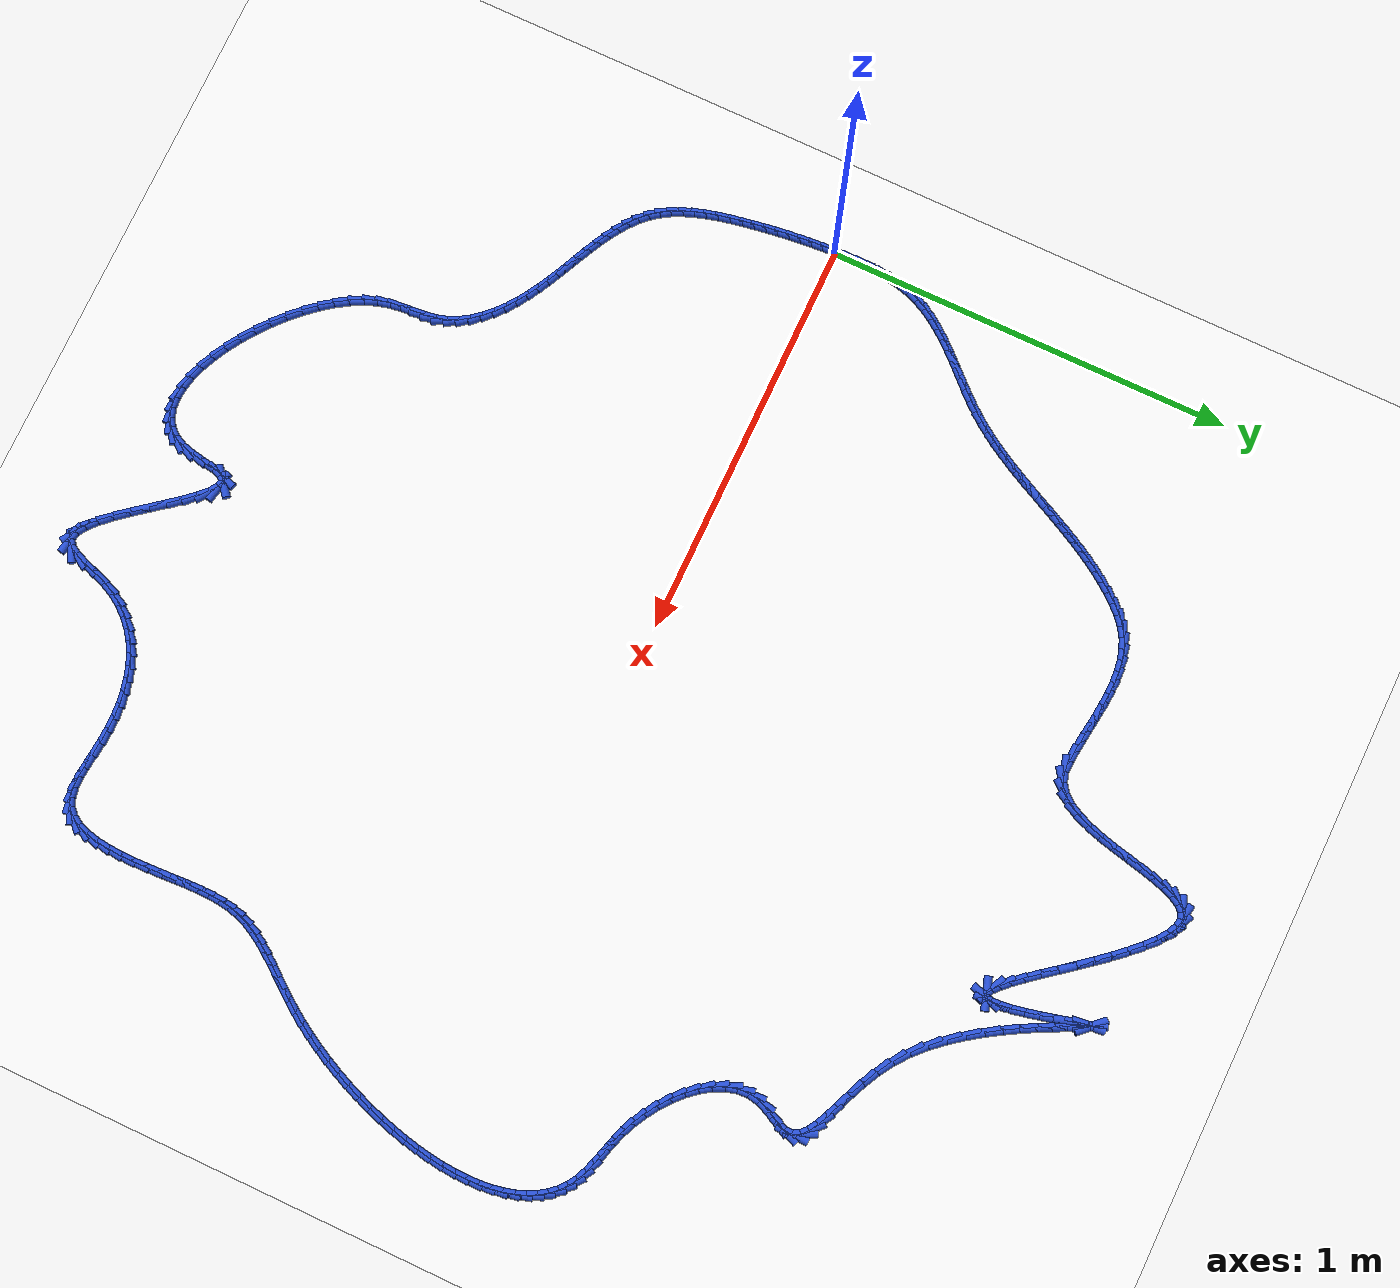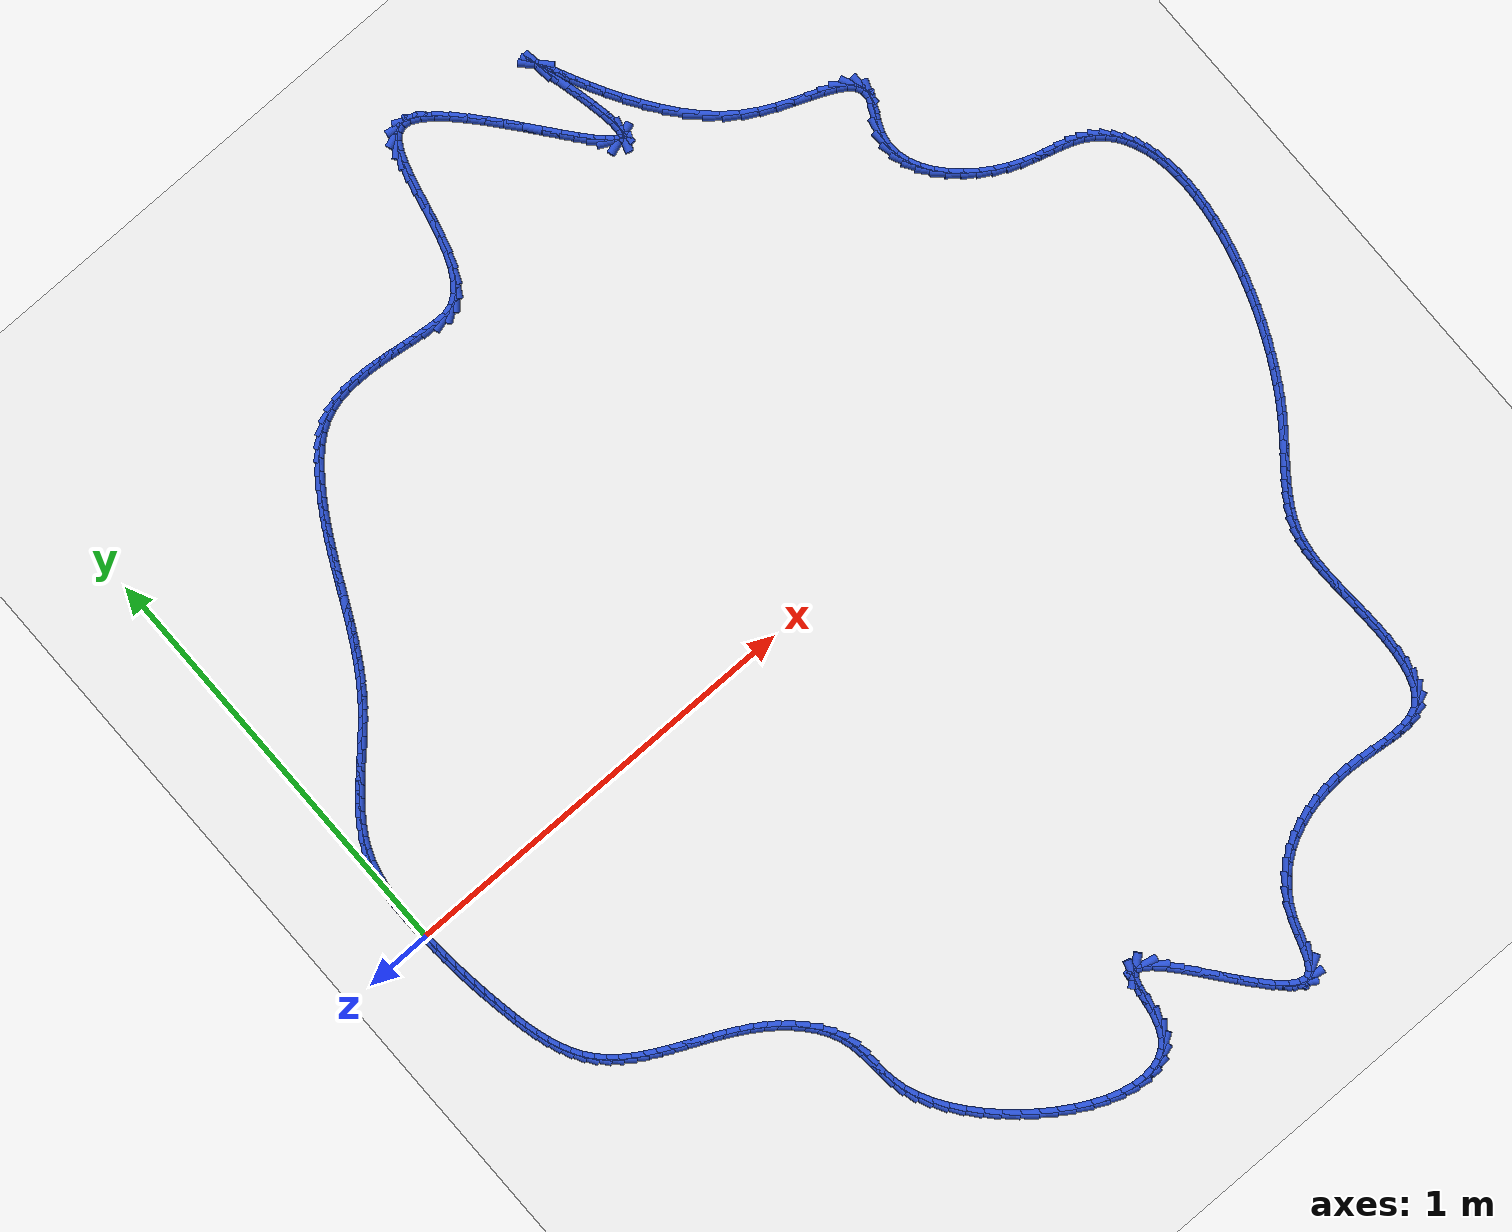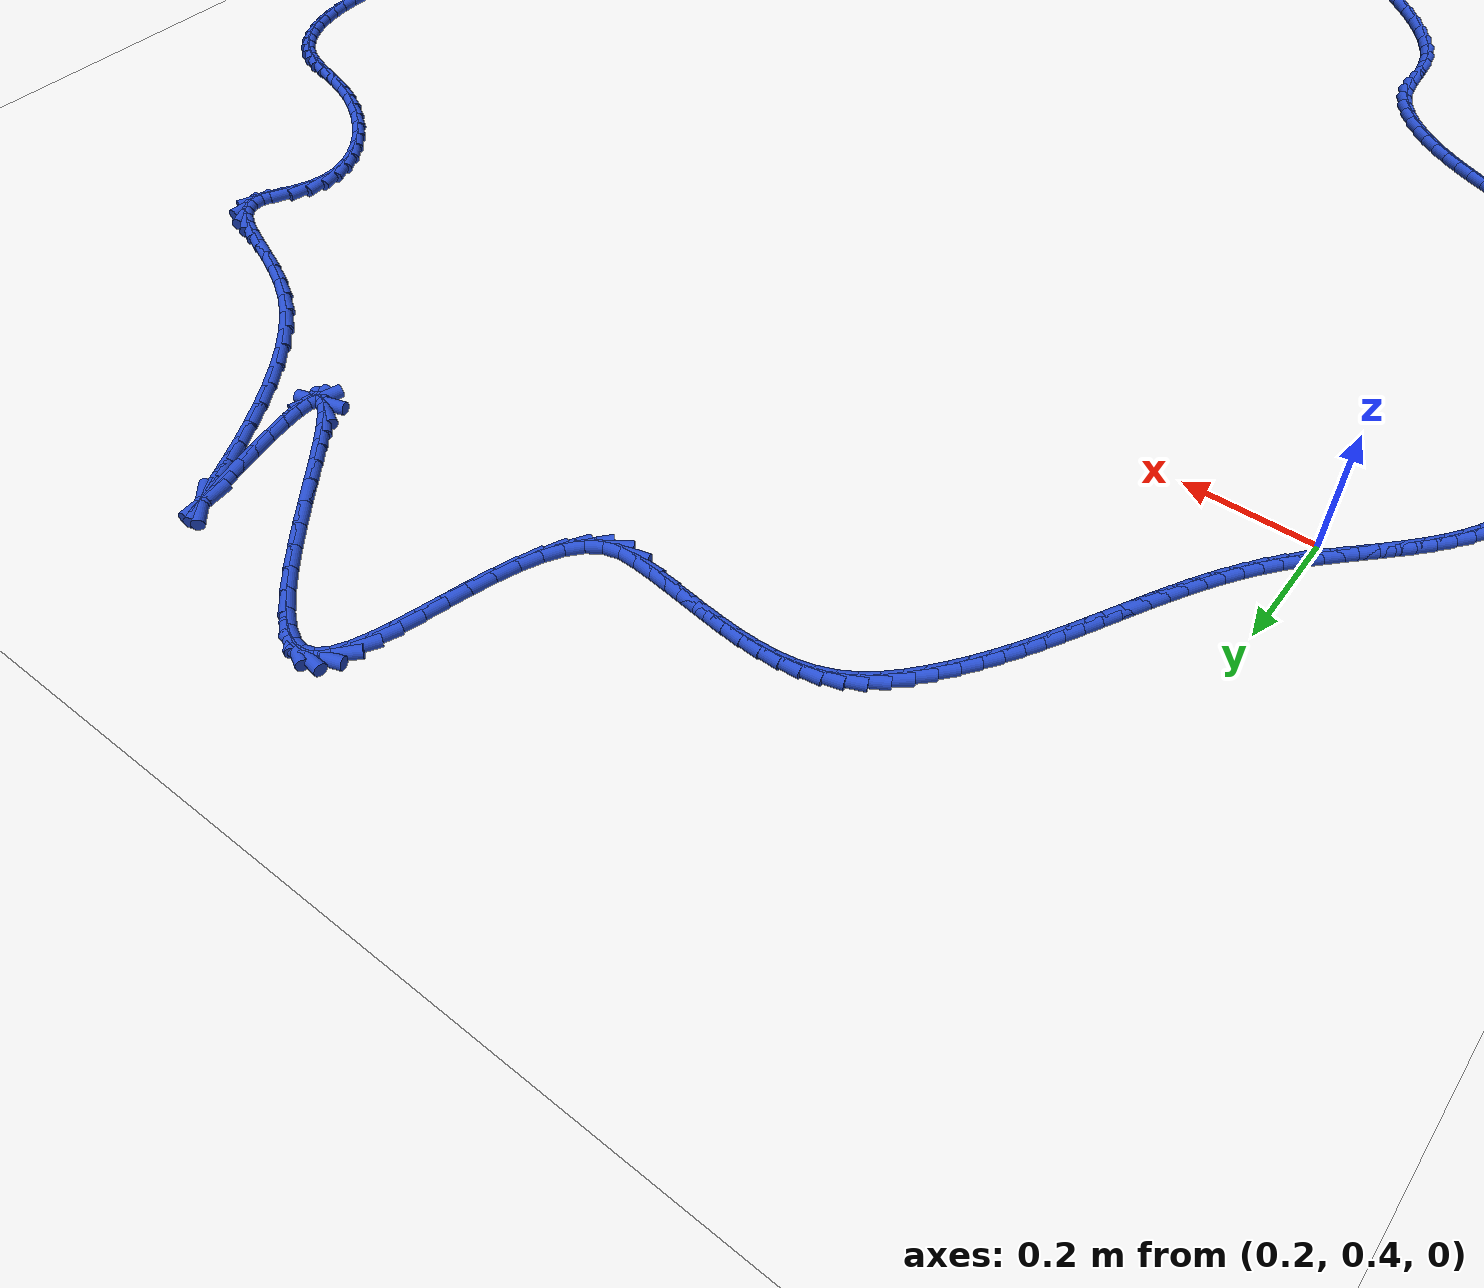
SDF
<sdf version="1.6">
 <world name="default">
  <light name="sun" type="directional">
   <pose>0 0 10 0 -0 0</pose>
   <diffuse>0.8 0.8 0.8 1</diffuse>
   <specular>0.2 0.2 0.2 1</specular>
   <attenuation>
    <range>1000</range>
    <constant>0.9</constant>
    <linear>0.01</linear>
    <quadratic>0.001</quadratic>
   </attenuation>
   <direction>-0.5 0.1 -0.9</direction>
  </light>
  <model name="ground_plane">
   <static>1</static>
   <link name="link">
    <collision name="collision">
     <geometry><plane><normal>0 0 1</normal><size>100 100</size></plane></geometry>
     <surface><friction><ode><mu>100</mu><mu2>50</mu2></ode></friction></surface>
    </collision>
    <visual name="visual">
     <cast_shadows>0</cast_shadows>
     <geometry><plane><normal>0 0 1</normal><size>100 100</size></plane></geometry>
     <material>
      <script><uri>file://media/materials/scripts/gazebo.material</uri><name>Gazebo/WhiteGlow</name></script>
     </material>
    </visual>
   </link>
  </model>
  <gravity>0 0 -9.8</gravity>
  <magnetic_field>6e-06 2.3e-05 -4.2e-05</magnetic_field>
  <atmosphere type="adiabatic"/>
  <physics name="default_physics" default="0" type="ode">
   <max_step_size>0.001</max_step_size>
   <real_time_factor>1</real_time_factor>
   <real_time_update_rate>1000</real_time_update_rate>
  </physics>
  <scene><ambient>0.4 0.4 0.4 1</ambient><background>0.7 0.7 0.7 1</background><shadows>1</shadows></scene>
  <spherical_coordinates>
   <surface_model>EARTH_WGS84</surface_model>
   <latitude_deg>0</latitude_deg>
   <longitude_deg>0</longitude_deg>
   <elevation>0</elevation>
   <heading_deg>0</heading_deg>
  </spherical_coordinates>
  <model name="line">
   <link name="link_0">
    <pose>-7.765598060427426e-18 6.938893903907228e-18 0.01 0 1.57 -1.5346862681462767</pose>
    <collision name="collision">
     <geometry><cylinder><radius>0.01</radius><length>0.08</length></cylinder></geometry>
    </collision>
    <visual name="visual">
     <material>
      <script><name>Gazebo/Blue</name><uri>file://media/materials/scripts/gazebo.material</uri></script>
     </material>
     <geometry><cylinder><radius>0.01</radius><length>0.08</length></cylinder></geometry>
    </visual>
   </link>
   <link name="link_1">
    <pose>-0.0010485585645357792 0.02902523044638611 0.01 0 1.57 -1.5600147824058368</pose>
    <collision name="collision">
     <geometry><cylinder><radius>0.01</radius><length>0.08</length></cylinder></geometry>
    </collision>
    <visual name="visual">
     <material>
      <script><name>Gazebo/Blue</name><uri>file://media/materials/scripts/gazebo.material</uri></script>
     </material>
     <geometry><cylinder><radius>0.01</radius><length>0.08</length></cylinder></geometry>
    </visual>
   </link>
   <link name="link_2">
    <pose>-0.0013635878956722515 0.05824341229114953 0.01 0 1.57 1.5468679772924028</pose>
    <collision name="collision">
     <geometry><cylinder><radius>0.01</radius><length>0.08</length></cylinder></geometry>
    </collision>
    <visual name="visual">
     <material>
      <script><name>Gazebo/Blue</name><uri>file://media/materials/scripts/gazebo.material</uri></script>
     </material>
     <geometry><cylinder><radius>0.01</radius><length>0.08</length></cylinder></geometry>
    </visual>
   </link>
   <link name="link_3">
    <pose>-0.0006648223881323449 0.08744025009533356 0.01 0 1.57 1.5020944176287139</pose>
    <collision name="collision">
     <geometry><cylinder><radius>0.01</radius><length>0.08</length></cylinder></geometry>
    </collision>
    <visual name="visual">
     <material>
      <script><name>Gazebo/Blue</name><uri>file://media/materials/scripts/gazebo.material</uri></script>
     </material>
     <geometry><cylinder><radius>0.01</radius><length>0.08</length></cylinder></geometry>
    </visual>
   </link>
   <link name="link_4">
    <pose>0.00132800356336102 0.11640144841998161 0.01 0 1.57 1.4463293020893944</pose>
    <collision name="collision">
     <geometry><cylinder><radius>0.01</radius><length>0.08</length></cylinder></geometry>
    </collision>
    <visual name="visual">
     <material>
      <script><name>Gazebo/Blue</name><uri>file://media/materials/scripts/gazebo.material</uri></script>
     </material>
     <geometry><cylinder><radius>0.01</radius><length>0.08</length></cylinder></geometry>
    </visual>
   </link>
   <link name="link_5">
    <pose>0.004895155564084923 0.14491271182613702 0.01 0 1.57 1.3785046252209874</pose>
    <collision name="collision">
     <geometry><cylinder><radius>0.01</radius><length>0.08</length></cylinder></geometry>
    </collision>
    <visual name="visual">
     <material>
      <script><name>Gazebo/Blue</name><uri>file://media/materials/scripts/gazebo.material</uri></script>
     </material>
     <geometry><cylinder><radius>0.01</radius><length>0.08</length></cylinder></geometry>
    </visual>
   </link>
   <link name="link_6">
    <pose>0.010316899219316444 0.17275974487484322 0.01 0 1.57 1.297601307586867</pose>
    <collision name="collision">
     <geometry><cylinder><radius>0.01</radius><length>0.08</length></cylinder></geometry>
    </collision>
    <visual name="visual">
     <material>
      <script><name>Gazebo/Blue</name><uri>file://media/materials/scripts/gazebo.material</uri></script>
     </material>
     <geometry><cylinder><radius>0.01</radius><length>0.08</length></cylinder></geometry>
    </visual>
   </link>
   <link name="link_7">
    <pose>0.017873500134332667 0.19972825212714362 0.01 0 1.57 1.2032728674085313</pose>
    <collision name="collision">
     <geometry><cylinder><radius>0.01</radius><length>0.08</length></cylinder></geometry>
    </collision>
    <visual name="visual">
     <material>
      <script><name>Gazebo/Blue</name><uri>file://media/materials/scripts/gazebo.material</uri></script>
     </material>
     <geometry><cylinder><radius>0.01</radius><length>0.08</length></cylinder></geometry>
    </visual>
   </link>
   <link name="link_8">
    <pose>0.02783782909656303 0.22560849781510114 0.01 0 1.57 1.106756338111016</pose>
    <collision name="collision">
     <geometry><cylinder><radius>0.01</radius><length>0.08</length></cylinder></geometry>
    </collision>
    <visual name="visual">
     <material>
      <script><name>Gazebo/Blue</name><uri>file://media/materials/scripts/gazebo.material</uri></script>
     </material>
     <geometry><cylinder><radius>0.01</radius><length>0.08</length></cylinder></geometry>
    </visual>
   </link>
   <link name="link_9">
    <pose>0.040221605151668866 0.2503517732647848 0.01 0 1.57 1.0231207383510295</pose>
    <collision name="collision">
     <geometry><cylinder><radius>0.01</radius><length>0.08</length></cylinder></geometry>
    </collision>
    <visual name="visual">
     <material>
      <script><name>Gazebo/Blue</name><uri>file://media/materials/scripts/gazebo.material</uri></script>
     </material>
     <geometry><cylinder><radius>0.01</radius><length>0.08</length></cylinder></geometry>
    </visual>
   </link>
   <link name="link_10">
    <pose>0.054711789538546045 0.2741096166224646 0.01 0 1.57 0.954018145685561</pose>
    <collision name="collision">
     <geometry><cylinder><radius>0.01</radius><length>0.08</length></cylinder></geometry>
    </collision>
    <visual name="visual">
     <material>
      <script><name>Gazebo/Blue</name><uri>file://media/materials/scripts/gazebo.material</uri></script>
     </material>
     <geometry><cylinder><radius>0.01</radius><length>0.08</length></cylinder></geometry>
    </visual>
   </link>
   <link name="link_11">
    <pose>0.07097503768646142 0.29704608666894217 0.01 0 1.57 0.8993581174436116</pose>
    <collision name="collision">
     <geometry><cylinder><radius>0.01</radius><length>0.08</length></cylinder></geometry>
    </collision>
    <visual name="visual">
     <material>
      <script><name>Gazebo/Blue</name><uri>file://media/materials/scripts/gazebo.material</uri></script>
     </material>
     <geometry><cylinder><radius>0.01</radius><length>0.08</length></cylinder></geometry>
    </visual>
   </link>
   <link name="link_12">
    <pose>0.08867800502468182 0.31932524218501945 0.01 0 1.57 0.8585900104488771</pose>
    <collision name="collision">
     <geometry><cylinder><radius>0.01</radius><length>0.08</length></cylinder></geometry>
    </collision>
    <visual name="visual">
     <material>
      <script><name>Gazebo/Blue</name><uri>file://media/materials/scripts/gazebo.material</uri></script>
     </material>
     <geometry><cylinder><radius>0.01</radius><length>0.08</length></cylinder></geometry>
    </visual>
   </link>
   <link name="link_13">
    <pose>0.10748734698247402 0.3411111419514979 0.01 0 1.57 0.8310383050136876</pose>
    <collision name="collision">
     <geometry><cylinder><radius>0.01</radius><length>0.08</length></cylinder></geometry>
    </collision>
    <visual name="visual">
     <material>
      <script><name>Gazebo/Blue</name><uri>file://media/materials/scripts/gazebo.material</uri></script>
     </material>
     <geometry><cylinder><radius>0.01</radius><length>0.08</length></cylinder></geometry>
    </visual>
   </link>
   <link name="link_14">
    <pose>0.12706971898910494 0.36256784474917947 0.01 0 1.57 0.8161170331663543</pose>
    <collision name="collision">
     <geometry><cylinder><radius>0.01</radius><length>0.08</length></cylinder></geometry>
    </collision>
    <visual name="visual">
     <material>
      <script><name>Gazebo/Blue</name><uri>file://media/materials/scripts/gazebo.material</uri></script>
     </material>
     <geometry><cylinder><radius>0.01</radius><length>0.08</length></cylinder></geometry>
    </visual>
   </link>
   <link name="link_15">
    <pose>0.14709177647384136 0.3838594093588659 0.01 0 1.57 0.8134477370516059</pose>
    <collision name="collision">
     <geometry><cylinder><radius>0.01</radius><length>0.08</length></cylinder></geometry>
    </collision>
    <visual name="visual">
     <material>
      <script><name>Gazebo/Blue</name><uri>file://media/materials/scripts/gazebo.material</uri></script>
     </material>
     <geometry><cylinder><radius>0.01</radius><length>0.08</length></cylinder></geometry>
    </visual>
   </link>
   <link name="link_16">
    <pose>0.1672201748659501 0.40514989456135897 0.01 0 1.57 0.8229110886200798</pose>
    <collision name="collision">
     <geometry><cylinder><radius>0.01</radius><length>0.08</length></cylinder></geometry>
    </collision>
    <visual name="visual">
     <material>
      <script><name>Gazebo/Blue</name><uri>file://media/materials/scripts/gazebo.material</uri></script>
     </material>
     <geometry><cylinder><radius>0.01</radius><length>0.08</length></cylinder></geometry>
    </visual>
   </link>
   <link name="link_17">
    <pose>0.18712156959469792 0.42660335913746006 0.01 0 1.57 0.84465178208153</pose>
    <collision name="collision">
     <geometry><cylinder><radius>0.01</radius><length>0.08</length></cylinder></geometry>
    </collision>
    <visual name="visual">
     <material>
      <script><name>Gazebo/Blue</name><uri>file://media/materials/scripts/gazebo.material</uri></script>
     </material>
     <geometry><cylinder><radius>0.01</radius><length>0.08</length></cylinder></geometry>
    </visual>
   </link>
   <link name="link_18">
    <pose>0.20646261608935187 0.4483838618679715 0.01 0 1.57 0.8790407648653263</pose>
    <collision name="collision">
     <geometry><cylinder><radius>0.01</radius><length>0.08</length></cylinder></geometry>
    </collision>
    <visual name="visual">
     <material>
      <script><name>Gazebo/Blue</name><uri>file://media/materials/scripts/gazebo.material</uri></script>
     </material>
     <geometry><cylinder><radius>0.01</radius><length>0.08</length></cylinder></geometry>
    </visual>
   </link>
   <link name="link_19">
    <pose>0.22490999089616565 0.4706554510278358 0.01 0 1.57 0.9229865366737087</pose>
    <collision name="collision">
     <geometry><cylinder><radius>0.01</radius><length>0.08</length></cylinder></geometry>
    </collision>
    <visual name="visual">
     <material>
      <script><name>Gazebo/Blue</name><uri>file://media/materials/scripts/gazebo.material</uri></script>
     </material>
     <geometry><cylinder><radius>0.01</radius><length>0.08</length></cylinder></geometry>
    </visual>
   </link>
   <link name="link_20">
    <pose>0.24222446091529953 0.4935353642381594 0.01 0 1.57 0.9647569641755463</pose>
    <collision name="collision">
     <geometry><cylinder><radius>0.01</radius><length>0.08</length></cylinder></geometry>
    </collision>
    <visual name="visual">
     <material>
      <script><name>Gazebo/Blue</name><uri>file://media/materials/scripts/gazebo.material</uri></script>
     </material>
     <geometry><cylinder><radius>0.01</radius><length>0.08</length></cylinder></geometry>
    </visual>
   </link>
   <link name="link_21">
    <pose>0.25847702693704133 0.5169864954425484 0.01 0 1.57 1.0016227718409108</pose>
    <collision name="collision">
     <geometry><cylinder><radius>0.01</radius><length>0.08</length></cylinder></geometry>
    </collision>
    <visual name="visual">
     <material>
      <script><name>Gazebo/Blue</name><uri>file://media/materials/scripts/gazebo.material</uri></script>
     </material>
     <geometry><cylinder><radius>0.01</radius><length>0.08</length></cylinder></geometry>
    </visual>
   </link>
   <link name="link_22">
    <pose>0.27380253844907126 0.5409399733807645 0.01 0 1.57 1.0333630666071587</pose>
    <collision name="collision">
     <geometry><cylinder><radius>0.01</radius><length>0.08</length></cylinder></geometry>
    </collision>
    <visual name="visual">
     <material>
      <script><name>Gazebo/Blue</name><uri>file://media/materials/scripts/gazebo.material</uri></script>
     </material>
     <geometry><cylinder><radius>0.01</radius><length>0.08</length></cylinder></geometry>
    </visual>
   </link>
   <link name="link_23">
    <pose>0.2883358449390694 0.56532692679257 0.01 0 1.57 1.059844360493518</pose>
    <collision name="collision">
     <geometry><cylinder><radius>0.01</radius><length>0.08</length></cylinder></geometry>
    </collision>
    <visual name="visual">
     <material>
      <script><name>Gazebo/Blue</name><uri>file://media/materials/scripts/gazebo.material</uri></script>
     </material>
     <geometry><cylinder><radius>0.01</radius><length>0.08</length></cylinder></geometry>
    </visual>
   </link>
   <link name="link_24">
    <pose>0.3022117958947165 0.5900784844177276 0.01 0 1.57 1.0809978505442215</pose>
    <collision name="collision">
     <geometry><cylinder><radius>0.01</radius><length>0.08</length></cylinder></geometry>
    </collision>
    <visual name="visual">
     <material>
      <script><name>Gazebo/Blue</name><uri>file://media/materials/scripts/gazebo.material</uri></script>
     </material>
     <geometry><cylinder><radius>0.01</radius><length>0.08</length></cylinder></geometry>
    </visual>
   </link>
   <link name="link_25">
    <pose>0.31556524080369247 0.6151257749959993 0.01 0 1.57 1.0967982440395854</pose>
    <collision name="collision">
     <geometry><cylinder><radius>0.01</radius><length>0.08</length></cylinder></geometry>
    </collision>
    <visual name="visual">
     <material>
      <script><name>Gazebo/Blue</name><uri>file://media/materials/scripts/gazebo.material</uri></script>
     </material>
     <geometry><cylinder><radius>0.01</radius><length>0.08</length></cylinder></geometry>
    </visual>
   </link>
   <link name="link_26">
    <pose>0.3285310291536775 0.640399927267147 0.01 0 1.57 1.107245924653396</pose>
    <collision name="collision">
     <geometry><cylinder><radius>0.01</radius><length>0.08</length></cylinder></geometry>
    </collision>
    <visual name="visual">
     <material>
      <script><name>Gazebo/Blue</name><uri>file://media/materials/scripts/gazebo.material</uri></script>
     </material>
     <geometry><cylinder><radius>0.01</radius><length>0.08</length></cylinder></geometry>
    </visual>
   </link>
   <link name="link_27">
    <pose>0.34124401043235203 0.6658320699709334 0.01 0 1.57 1.1123533730437685</pose>
    <collision name="collision">
     <geometry><cylinder><radius>0.01</radius><length>0.08</length></cylinder></geometry>
    </collision>
    <visual name="visual">
     <material>
      <script><name>Gazebo/Blue</name><uri>file://media/materials/scripts/gazebo.material</uri></script>
     </material>
     <geometry><cylinder><radius>0.01</radius><length>0.08</length></cylinder></geometry>
    </visual>
   </link>
   <link name="link_28">
    <pose>0.35383903412739637 0.6913533318471204 0.01 0 1.57 1.1121361780249635</pose>
    <collision name="collision">
     <geometry><cylinder><radius>0.01</radius><length>0.08</length></cylinder></geometry>
    </collision>
    <visual name="visual">
     <material>
      <script><name>Gazebo/Blue</name><uri>file://media/materials/scripts/gazebo.material</uri></script>
     </material>
     <geometry><cylinder><radius>0.01</radius><length>0.08</length></cylinder></geometry>
    </visual>
   </link>
   <link name="link_29">
    <pose>0.36645094972649067 0.7168948416354702 0.01 0 1.57 1.1066086731521811</pose>
    <collision name="collision">
     <geometry><cylinder><radius>0.01</radius><length>0.08</length></cylinder></geometry>
    </collision>
    <visual name="visual">
     <material>
      <script><name>Gazebo/Blue</name><uri>file://media/materials/scripts/gazebo.material</uri></script>
     </material>
     <geometry><cylinder><radius>0.01</radius><length>0.08</length></cylinder></geometry>
    </visual>
   </link>
   <link name="link_30">
    <pose>0.37921460671731505 0.7423877280757453 0.01 0 1.57 1.09578412580983</pose>
    <collision name="collision">
     <geometry><cylinder><radius>0.01</radius><length>0.08</length></cylinder></geometry>
    </collision>
    <visual name="visual">
     <material>
      <script><name>Gazebo/Blue</name><uri>file://media/materials/scripts/gazebo.material</uri></script>
     </material>
     <geometry><cylinder><radius>0.01</radius><length>0.08</length></cylinder></geometry>
    </visual>
   </link>
   <link name="link_31">
    <pose>0.39226485458755 0.7677631199077075 0.01 0 1.57 1.0796793932819586</pose>
    <collision name="collision">
     <geometry><cylinder><radius>0.01</radius><length>0.08</length></cylinder></geometry>
    </collision>
    <visual name="visual">
     <material>
      <script><name>Gazebo/Blue</name><uri>file://media/materials/scripts/gazebo.material</uri></script>
     </material>
     <geometry><cylinder><radius>0.01</radius><length>0.08</length></cylinder></geometry>
    </visual>
   </link>
   <link name="link_32">
    <pose>0.4057365428248756 0.7929521458711193 0.01 0 1.57 1.0583239445686288</pose>
    <collision name="collision">
     <geometry><cylinder><radius>0.01</radius><length>0.08</length></cylinder></geometry>
    </collision>
    <visual name="visual">
     <material>
      <script><name>Gazebo/Blue</name><uri>file://media/materials/scripts/gazebo.material</uri></script>
     </material>
     <geometry><cylinder><radius>0.01</radius><length>0.08</length></cylinder></geometry>
    </visual>
   </link>
   <link name="link_33">
    <pose>0.4197645209169723 0.8178859347057429 0.01 0 1.57 1.0317730345256997</pose>
    <collision name="collision">
     <geometry><cylinder><radius>0.01</radius><length>0.08</length></cylinder></geometry>
    </collision>
    <visual name="visual">
     <material>
      <script><name>Gazebo/Blue</name><uri>file://media/materials/scripts/gazebo.material</uri></script>
     </material>
     <geometry><cylinder><radius>0.01</radius><length>0.08</length></cylinder></geometry>
    </visual>
   </link>
   <link name="link_34">
    <pose>0.43448363835152015 0.8424956151513404 0.01 0 1.57 1.0001245244347499</pose>
    <collision name="collision">
     <geometry><cylinder><radius>0.01</radius><length>0.08</length></cylinder></geometry>
    </collision>
    <visual name="visual">
     <material>
      <script><name>Gazebo/Blue</name><uri>file://media/materials/scripts/gazebo.material</uri></script>
     </material>
     <geometry><cylinder><radius>0.01</radius><length>0.08</length></cylinder></geometry>
    </visual>
   </link>
   <link name="link_35">
    <pose>0.45002874461619946 0.866712315947674 0.01 0 1.57 0.9635383113401117</pose>
    <collision name="collision">
     <geometry><cylinder><radius>0.01</radius><length>0.08</length></cylinder></geometry>
    </collision>
    <visual name="visual">
     <material>
      <script><name>Gazebo/Blue</name><uri>file://media/materials/scripts/gazebo.material</uri></script>
     </material>
     <geometry><cylinder><radius>0.01</radius><length>0.08</length></cylinder></geometry>
    </visual>
   </link>
   <link name="link_36">
    <pose>0.4665346891986907 0.8904671658345061 0.01 0 1.57 0.9222548509347372</pose>
    <collision name="collision">
     <geometry><cylinder><radius>0.01</radius><length>0.08</length></cylinder></geometry>
    </collision>
    <visual name="visual">
     <material>
      <script><name>Gazebo/Blue</name><uri>file://media/materials/scripts/gazebo.material</uri></script>
     </material>
     <geometry><cylinder><radius>0.01</radius><length>0.08</length></cylinder></geometry>
    </visual>
   </link>
   <link name="link_37">
    <pose>0.48413632059294864 0.9136912099941349 0.01 0 1.57 0.87240958952419</pose>
    <collision name="collision">
     <geometry><cylinder><radius>0.01</radius><length>0.08</length></cylinder></geometry>
    </collision>
    <visual name="visual">
     <material>
      <script><name>Gazebo/Blue</name><uri>file://media/materials/scripts/gazebo.material</uri></script>
     </material>
     <geometry><cylinder><radius>0.01</radius><length>0.08</length></cylinder></geometry>
    </visual>
   </link>
   <link name="link_38">
    <pose>0.5029661638170291 0.9361201239490611 0.01 0 1.57 0.7993963007662317</pose>
    <collision name="collision">
     <geometry><cylinder><radius>0.01</radius><length>0.08</length></cylinder></geometry>
    </collision>
    <visual name="visual">
     <material>
      <script><name>Gazebo/Blue</name><uri>file://media/materials/scripts/gazebo.material</uri></script>
     </material>
     <geometry><cylinder><radius>0.01</radius><length>0.08</length></cylinder></geometry>
    </visual>
   </link>
   <link name="link_39">
    <pose>0.5231494530218614 0.9568765300670227 0.01 0 1.57 0.6957220276804327</pose>
    <collision name="collision">
     <geometry><cylinder><radius>0.01</radius><length>0.08</length></cylinder></geometry>
    </collision>
    <visual name="visual">
     <material>
      <script><name>Gazebo/Blue</name><uri>file://media/materials/scripts/gazebo.material</uri></script>
     </material>
     <geometry><cylinder><radius>0.01</radius><length>0.08</length></cylinder></geometry>
    </visual>
   </link>
   <link name="link_40">
    <pose>0.5448099960378696 0.9749631184401399 0.01 0 1.57 0.5558762434495466</pose>
    <collision name="collision">
     <geometry><cylinder><radius>0.01</radius><length>0.08</length></cylinder></geometry>
    </collision>
    <visual name="visual">
     <material>
      <script><name>Gazebo/Blue</name><uri>file://media/materials/scripts/gazebo.material</uri></script>
     </material>
     <geometry><cylinder><radius>0.01</radius><length>0.08</length></cylinder></geometry>
    </visual>
   </link>
   <link name="link_41">
    <pose>0.5680656244115422 0.9894099718206363 0.01 0 1.57 0.40118058593164074</pose>
    <collision name="collision">
     <geometry><cylinder><radius>0.01</radius><length>0.08</length></cylinder></geometry>
    </collision>
    <visual name="visual">
     <material>
      <script><name>Gazebo/Blue</name><uri>file://media/materials/scripts/gazebo.material</uri></script>
     </material>
     <geometry><cylinder><radius>0.01</radius><length>0.08</length></cylinder></geometry>
    </visual>
   </link>
   <link name="link_42">
    <pose>0.5928835840646357 0.9999373913103434 0.01 0 1.57 0.2630922294704013</pose>
    <collision name="collision">
     <geometry><cylinder><radius>0.01</radius><length>0.08</length></cylinder></geometry>
    </collision>
    <visual name="visual">
     <material>
      <script><name>Gazebo/Blue</name><uri>file://media/materials/scripts/gazebo.material</uri></script>
     </material>
     <geometry><cylinder><radius>0.01</radius><length>0.08</length></cylinder></geometry>
    </visual>
   </link>
   <link name="link_43">
    <pose>0.6190728574797417 1.0069910880891046 0.01 0 1.57 0.14731021760152851</pose>
    <collision name="collision">
     <geometry><cylinder><radius>0.01</radius><length>0.08</length></cylinder></geometry>
    </collision>
    <visual name="visual">
     <material>
      <script><name>Gazebo/Blue</name><uri>file://media/materials/scripts/gazebo.material</uri></script>
     </material>
     <geometry><cylinder><radius>0.01</radius><length>0.08</length></cylinder></geometry>
    </visual>
   </link>
   <link name="link_44">
    <pose>0.6464349141021115 1.011051209799362 0.01 0 1.57 0.05452936577938574</pose>
    <collision name="collision">
     <geometry><cylinder><radius>0.01</radius><length>0.08</length></cylinder></geometry>
    </collision>
    <visual name="visual">
     <material>
      <script><name>Gazebo/Blue</name><uri>file://media/materials/scripts/gazebo.material</uri></script>
     </material>
     <geometry><cylinder><radius>0.01</radius><length>0.08</length></cylinder></geometry>
    </visual>
   </link>
   <link name="link_45">
    <pose>0.6747712233769956 1.012597904083557 0.01 0 1.57 -0.01671268449121818</pose>
    <collision name="collision">
     <geometry><cylinder><radius>0.01</radius><length>0.08</length></cylinder></geometry>
    </collision>
    <visual name="visual">
     <material>
      <script><name>Gazebo/Blue</name><uri>file://media/materials/scripts/gazebo.material</uri></script>
     </material>
     <geometry><cylinder><radius>0.01</radius><length>0.08</length></cylinder></geometry>
    </visual>
   </link>
   <link name="link_46">
    <pose>0.703883254749645 1.012111318584132 0.01 0 1.57 -0.06859450465147793</pose>
    <collision name="collision">
     <geometry><cylinder><radius>0.01</radius><length>0.08</length></cylinder></geometry>
    </collision>
    <visual name="visual">
     <material>
      <script><name>Gazebo/Blue</name><uri>file://media/materials/scripts/gazebo.material</uri></script>
     </material>
     <geometry><cylinder><radius>0.01</radius><length>0.08</length></cylinder></geometry>
    </visual>
   </link>
   <link name="link_47">
    <pose>0.7335724776653103 1.010071600943527 0.01 0 1.57 -0.10315503395575393</pose>
    <collision name="collision">
     <geometry><cylinder><radius>0.01</radius><length>0.08</length></cylinder></geometry>
    </collision>
    <visual name="visual">
     <material>
      <script><name>Gazebo/Blue</name><uri>file://media/materials/scripts/gazebo.material</uri></script>
     </material>
     <geometry><cylinder><radius>0.01</radius><length>0.08</length></cylinder></geometry>
    </visual>
   </link>
   <link name="link_48">
    <pose>0.7636403615692429 1.0069588988041849 0.01 0 1.57 -0.12189782490905618</pose>
    <collision name="collision">
     <geometry><cylinder><radius>0.01</radius><length>0.08</length></cylinder></geometry>
    </collision>
    <visual name="visual">
     <material>
      <script><name>Gazebo/Blue</name><uri>file://media/materials/scripts/gazebo.material</uri></script>
     </material>
     <geometry><cylinder><radius>0.01</radius><length>0.08</length></cylinder></geometry>
    </visual>
   </link>
   <link name="link_49">
    <pose>0.7938883759066931 1.003253359808547 0.01 0 1.57 -0.12564221077426754</pose>
    <collision name="collision">
     <geometry><cylinder><radius>0.01</radius><length>0.08</length></cylinder></geometry>
    </collision>
    <visual name="visual">
     <material>
      <script><name>Gazebo/Blue</name><uri>file://media/materials/scripts/gazebo.material</uri></script>
     </material>
     <geometry><cylinder><radius>0.01</radius><length>0.08</length></cylinder></geometry>
    </visual>
   </link>
   <link name="link_50">
    <pose>0.8241179901229124 0.9994351315990544 0.01 0 1.57 -0.11447437510522215</pose>
    <collision name="collision">
     <geometry><cylinder><radius>0.01</radius><length>0.08</length></cylinder></geometry>
    </collision>
    <visual name="visual">
     <material>
      <script><name>Gazebo/Blue</name><uri>file://media/materials/scripts/gazebo.material</uri></script>
     </material>
     <geometry><cylinder><radius>0.01</radius><length>0.08</length></cylinder></geometry>
    </visual>
   </link>
   <link name="link_51">
    <pose>0.8541306736631509 0.9959843618181494 0.01 0 1.57 -0.08772722702425166</pose>
    <collision name="collision">
     <geometry><cylinder><radius>0.01</radius><length>0.08</length></cylinder></geometry>
    </collision>
    <visual name="visual">
     <material>
      <script><name>Gazebo/Blue</name><uri>file://media/materials/scripts/gazebo.material</uri></script>
     </material>
     <geometry><cylinder><radius>0.01</radius><length>0.08</length></cylinder></geometry>
    </visual>
   </link>
   <link name="link_52">
    <pose>0.8837278959726601 0.993381198108273 0.01 0 1.57 -0.01701527044721133</pose>
    <collision name="collision">
     <geometry><cylinder><radius>0.01</radius><length>0.08</length></cylinder></geometry>
    </collision>
    <visual name="visual">
     <material>
      <script><name>Gazebo/Blue</name><uri>file://media/materials/scripts/gazebo.material</uri></script>
     </material>
     <geometry><cylinder><radius>0.01</radius><length>0.08</length></cylinder></geometry>
    </visual>
   </link>
   <link name="link_53">
    <pose>0.9123358119783457 0.992894379698469 0.01 0 1.57 0.2726886236249422</pose>
    <collision name="collision">
     <geometry><cylinder><radius>0.01</radius><length>0.08</length></cylinder></geometry>
    </collision>
    <visual name="visual">
     <material>
      <script><name>Gazebo/Blue</name><uri>file://media/materials/scripts/gazebo.material</uri></script>
     </material>
     <geometry><cylinder><radius>0.01</radius><length>0.08</length></cylinder></geometry>
    </visual>
   </link>
   <link name="link_54">
    <pose>0.9373992751168906 0.999903498904146 0.01 0 1.57 0.6130740387735507</pose>
    <collision name="collision">
     <geometry><cylinder><radius>0.01</radius><length>0.08</length></cylinder></geometry>
    </collision>
    <visual name="visual">
     <material>
      <script><name>Gazebo/Blue</name><uri>file://media/materials/scripts/gazebo.material</uri></script>
     </material>
     <geometry><cylinder><radius>0.01</radius><length>0.08</length></cylinder></geometry>
    </visual>
   </link>
   <link name="link_55">
    <pose>0.9586350325758902 1.0148429476561867 0.01 0 1.57 0.8795695974295934</pose>
    <collision name="collision">
     <geometry><cylinder><radius>0.01</radius><length>0.08</length></cylinder></geometry>
    </collision>
    <visual name="visual">
     <material>
      <script><name>Gazebo/Blue</name><uri>file://media/materials/scripts/gazebo.material</uri></script>
     </material>
     <geometry><cylinder><radius>0.01</radius><length>0.08</length></cylinder></geometry>
    </visual>
   </link>
   <link name="link_56">
    <pose>0.976536888476006 1.0364792106758454 0.01 0 1.57 1.0635160704220663</pose>
    <collision name="collision">
     <geometry><cylinder><radius>0.01</radius><length>0.08</length></cylinder></geometry>
    </collision>
    <visual name="visual">
     <material>
      <script><name>Gazebo/Blue</name><uri>file://media/materials/scripts/gazebo.material</uri></script>
     </material>
     <geometry><cylinder><radius>0.01</radius><length>0.08</length></cylinder></geometry>
    </visual>
   </link>
   <link name="link_57">
    <pose>0.9915986469378985 1.063578772684376 0.01 0 1.57 1.185244704178459</pose>
    <collision name="collision">
     <geometry><cylinder><radius>0.01</radius><length>0.08</length></cylinder></geometry>
    </collision>
    <visual name="visual">
     <material>
      <script><name>Gazebo/Blue</name><uri>file://media/materials/scripts/gazebo.material</uri></script>
     </material>
     <geometry><cylinder><radius>0.01</radius><length>0.08</length></cylinder></geometry>
    </visual>
   </link>
   <link name="link_58">
    <pose>1.0043141120822288 1.0949081184030323 0.01 0 1.57 1.2643001150706743</pose>
    <collision name="collision">
     <geometry><cylinder><radius>0.01</radius><length>0.08</length></cylinder></geometry>
    </collision>
    <visual name="visual">
     <material>
      <script><name>Gazebo/Blue</name><uri>file://media/materials/scripts/gazebo.material</uri></script>
     </material>
     <geometry><cylinder><radius>0.01</radius><length>0.08</length></cylinder></geometry>
    </visual>
   </link>
   <link name="link_59">
    <pose>1.0151770880296582 1.1292337325530688 0.01 0 1.57 1.313282090881305</pose>
    <collision name="collision">
     <geometry><cylinder><radius>0.01</radius><length>0.08</length></cylinder></geometry>
    </collision>
    <visual name="visual">
     <material>
      <script><name>Gazebo/Blue</name><uri>file://media/materials/scripts/gazebo.material</uri></script>
     </material>
     <geometry><cylinder><radius>0.01</radius><length>0.08</length></cylinder></geometry>
    </visual>
   </link>
   <link name="link_60">
    <pose>1.0246813789008478 1.1653220998557392 0.01 0 1.57 1.3390975725473584</pose>
    <collision name="collision">
     <geometry><cylinder><radius>0.01</radius><length>0.08</length></cylinder></geometry>
    </collision>
    <visual name="visual">
     <material>
      <script><name>Gazebo/Blue</name><uri>file://media/materials/scripts/gazebo.material</uri></script>
     </material>
     <geometry><cylinder><radius>0.01</radius><length>0.08</length></cylinder></geometry>
    </visual>
   </link>
   <link name="link_61">
    <pose>1.0333207888164588 1.2019397050322986 0.01 0 1.57 1.3445093037787497</pose>
    <collision name="collision">
     <geometry><cylinder><radius>0.01</radius><length>0.08</length></cylinder></geometry>
    </collision>
    <visual name="visual">
     <material>
      <script><name>Gazebo/Blue</name><uri>file://media/materials/scripts/gazebo.material</uri></script>
     </material>
     <geometry><cylinder><radius>0.01</radius><length>0.08</length></cylinder></geometry>
    </visual>
   </link>
   <link name="link_62">
    <pose>1.0415891218971518 1.2378530328039998 0.01 0 1.57 1.328668057909878</pose>
    <collision name="collision">
     <geometry><cylinder><radius>0.01</radius><length>0.08</length></cylinder></geometry>
    </collision>
    <visual name="visual">
     <material>
      <script><name>Gazebo/Blue</name><uri>file://media/materials/scripts/gazebo.material</uri></script>
     </material>
     <geometry><cylinder><radius>0.01</radius><length>0.08</length></cylinder></geometry>
    </visual>
   </link>
   <link name="link_63">
    <pose>1.0499801822635881 1.2718285678920977 0.01 0 1.57 1.2863134789850907</pose>
    <collision name="collision">
     <geometry><cylinder><radius>0.01</radius><length>0.08</length></cylinder></geometry>
    </collision>
    <visual name="visual">
     <material>
      <script><name>Gazebo/Blue</name><uri>file://media/materials/scripts/gazebo.material</uri></script>
     </material>
     <geometry><cylinder><radius>0.01</radius><length>0.08</length></cylinder></geometry>
    </visual>
   </link>
   <link name="link_64">
    <pose>1.058987774036429 1.3026327950178458 0.01 0 1.57 1.2048007196171158</pose>
    <collision name="collision">
     <geometry><cylinder><radius>0.01</radius><length>0.08</length></cylinder></geometry>
    </collision>
    <visual name="visual">
     <material>
      <script><name>Gazebo/Blue</name><uri>file://media/materials/scripts/gazebo.material</uri></script>
     </material>
     <geometry><cylinder><radius>0.01</radius><length>0.08</length></cylinder></geometry>
    </visual>
   </link>
   <link name="link_65">
    <pose>1.0691057013363356 1.329032198902499 0.01 0 1.57 1.0567995523106515</pose>
    <collision name="collision">
     <geometry><cylinder><radius>0.01</radius><length>0.08</length></cylinder></geometry>
    </collision>
    <visual name="visual">
     <material>
      <script><name>Gazebo/Blue</name><uri>file://media/materials/scripts/gazebo.material</uri></script>
     </material>
     <geometry><cylinder><radius>0.01</radius><length>0.08</length></cylinder></geometry>
    </visual>
   </link>
   <link name="link_66">
    <pose>1.0808277682839686 1.3497932642673105 0.01 0 1.57 0.7878955523761453</pose>
    <collision name="collision">
     <geometry><cylinder><radius>0.01</radius><length>0.08</length></cylinder></geometry>
    </collision>
    <visual name="visual">
     <material>
      <script><name>Gazebo/Blue</name><uri>file://media/materials/scripts/gazebo.material</uri></script>
     </material>
     <geometry><cylinder><radius>0.01</radius><length>0.08</length></cylinder></geometry>
    </visual>
   </link>
   <link name="link_67">
    <pose>1.094647778999989 1.3636824758335344 0.01 0 1.57 0.3389187498005113</pose>
    <collision name="collision">
     <geometry><cylinder><radius>0.01</radius><length>0.08</length></cylinder></geometry>
    </collision>
    <visual name="visual">
     <material>
      <script><name>Gazebo/Blue</name><uri>file://media/materials/scripts/gazebo.material</uri></script>
     </material>
     <geometry><cylinder><radius>0.01</radius><length>0.08</length></cylinder></geometry>
    </visual>
   </link>
   <link name="link_68">
    <pose>1.1110589649936873 1.3694677601815661 0.01 0 1.57 -0.15165423664632643</pose>
    <collision name="collision">
     <geometry><cylinder><radius>0.01</radius><length>0.08</length></cylinder></geometry>
    </collision>
    <visual name="visual">
     <material>
      <script><name>Gazebo/Blue</name><uri>file://media/materials/scripts/gazebo.material</uri></script>
     </material>
     <geometry><cylinder><radius>0.01</radius><length>0.08</length></cylinder></geometry>
    </visual>
   </link>
   <link name="link_69">
    <pose>1.1303130361080307 1.3665252054472756 0.01 0 1.57 -0.459174871698221</pose>
    <collision name="collision">
     <geometry><cylinder><radius>0.01</radius><length>0.08</length></cylinder></geometry>
    </collision>
    <visual name="visual">
     <material>
      <script><name>Gazebo/Blue</name><uri>file://media/materials/scripts/gazebo.material</uri></script>
     </material>
     <geometry><cylinder><radius>0.01</radius><length>0.08</length></cylinder></geometry>
    </visual>
   </link>
   <link name="link_70">
    <pose>1.1520466438390968 1.3557796421491504 0.01 0 1.57 -0.6316998048241882</pose>
    <collision name="collision">
     <geometry><cylinder><radius>0.01</radius><length>0.08</length></cylinder></geometry>
    </collision>
    <visual name="visual">
     <material>
      <script><name>Gazebo/Blue</name><uri>file://media/materials/scripts/gazebo.material</uri></script>
     </material>
     <geometry><cylinder><radius>0.01</radius><length>0.08</length></cylinder></geometry>
    </visual>
   </link>
   <link name="link_71">
    <pose>1.1757999645843107 1.3383988290984274 0.01 0 1.57 -0.7342627828120555</pose>
    <collision name="collision">
     <geometry><cylinder><radius>0.01</radius><length>0.08</length></cylinder></geometry>
    </collision>
    <visual name="visual">
     <material>
      <script><name>Gazebo/Blue</name><uri>file://media/materials/scripts/gazebo.material</uri></script>
     </material>
     <geometry><cylinder><radius>0.01</radius><length>0.08</length></cylinder></geometry>
    </visual>
   </link>
   <link name="link_72">
    <pose>1.201113174741095 1.315550525106345 0.01 0 1.57 -0.7991154164352366</pose>
    <collision name="collision">
     <geometry><cylinder><radius>0.01</radius><length>0.08</length></cylinder></geometry>
    </collision>
    <visual name="visual">
     <material>
      <script><name>Gazebo/Blue</name><uri>file://media/materials/scripts/gazebo.material</uri></script>
     </material>
     <geometry><cylinder><radius>0.01</radius><length>0.08</length></cylinder></geometry>
    </visual>
   </link>
   <link name="link_73">
    <pose>1.2275264507068744 1.2884024889841414 0.01 0 1.57 -0.8416146879310283</pose>
    <collision name="collision">
     <geometry><cylinder><radius>0.01</radius><length>0.08</length></cylinder></geometry>
    </collision>
    <visual name="visual">
     <material>
      <script><name>Gazebo/Blue</name><uri>file://media/materials/scripts/gazebo.material</uri></script>
     </material>
     <geometry><cylinder><radius>0.01</radius><length>0.08</length></cylinder></geometry>
    </visual>
   </link>
   <link name="link_74">
    <pose>1.2545799688790722 1.2581224795430546 0.01 0 1.57 -0.8694371855828077</pose>
    <collision name="collision">
     <geometry><cylinder><radius>0.01</radius><length>0.08</length></cylinder></geometry>
    </collision>
    <visual name="visual">
     <material>
      <script><name>Gazebo/Blue</name><uri>file://media/materials/scripts/gazebo.material</uri></script>
     </material>
     <geometry><cylinder><radius>0.01</radius><length>0.08</length></cylinder></geometry>
    </visual>
   </link>
   <link name="link_75">
    <pose>1.2818139056551134 1.2258782555943233 0.01 0 1.57 -0.8864962085855524</pose>
    <collision name="collision">
     <geometry><cylinder><radius>0.01</radius><length>0.08</length></cylinder></geometry>
    </collision>
    <visual name="visual">
     <material>
      <script><name>Gazebo/Blue</name><uri>file://media/materials/scripts/gazebo.material</uri></script>
     </material>
     <geometry><cylinder><radius>0.01</radius><length>0.08</length></cylinder></geometry>
    </visual>
   </link>
   <link name="link_76">
    <pose>1.3087684374324198 1.1928375759491847 0.01 0 1.57 -0.8945676984376993</pose>
    <collision name="collision">
     <geometry><cylinder><radius>0.01</radius><length>0.08</length></cylinder></geometry>
    </collision>
    <visual name="visual">
     <material>
      <script><name>Gazebo/Blue</name><uri>file://media/materials/scripts/gazebo.material</uri></script>
     </material>
     <geometry><cylinder><radius>0.01</radius><length>0.08</length></cylinder></geometry>
    </visual>
   </link>
   <link name="link_77">
    <pose>1.334983740608417 1.160168199418877 0.01 0 1.57 -0.8938654774672163</pose>
    <collision name="collision">
     <geometry><cylinder><radius>0.01</radius><length>0.08</length></cylinder></geometry>
    </collision>
    <visual name="visual">
     <material>
      <script><name>Gazebo/Blue</name><uri>file://media/materials/scripts/gazebo.material</uri></script>
     </material>
     <geometry><cylinder><radius>0.01</radius><length>0.08</length></cylinder></geometry>
    </visual>
   </link>
   <link name="link_78">
    <pose>1.3599999915805292 1.129037884814639 0.01 0 1.57 -0.8829254231709356</pose>
    <collision name="collision">
     <geometry><cylinder><radius>0.01</radius><length>0.08</length></cylinder></geometry>
    </collision>
    <visual name="visual">
     <material>
      <script><name>Gazebo/Blue</name><uri>file://media/materials/scripts/gazebo.material</uri></script>
     </material>
     <geometry><cylinder><radius>0.01</radius><length>0.08</length></cylinder></geometry>
    </visual>
   </link>
   <link name="link_79">
    <pose>1.383357366746179 1.1006143909477075 0.01 0 1.57 -0.857568142804138</pose>
    <collision name="collision">
     <geometry><cylinder><radius>0.01</radius><length>0.08</length></cylinder></geometry>
    </collision>
    <visual name="visual">
     <material>
      <script><name>Gazebo/Blue</name><uri>file://media/materials/scripts/gazebo.material</uri></script>
     </material>
     <geometry><cylinder><radius>0.01</radius><length>0.08</length></cylinder></geometry>
    </visual>
   </link>
   <link name="link_80">
    <pose>1.404596042502791 1.076065476629322 0.01 0 1.57 -0.8075715201654636</pose>
    <collision name="collision">
     <geometry><cylinder><radius>0.01</radius><length>0.08</length></cylinder></geometry>
    </collision>
    <visual name="visual">
     <material>
      <script><name>Gazebo/Blue</name><uri>file://media/materials/scripts/gazebo.material</uri></script>
     </material>
     <geometry><cylinder><radius>0.01</radius><length>0.08</length></cylinder></geometry>
    </visual>
   </link>
   <link name="link_81">
    <pose>1.423256195247789 1.05655890067072 0.01 0 1.57 -0.7051605216147377</pose>
    <collision name="collision">
     <geometry><cylinder><radius>0.01</radius><length>0.08</length></cylinder></geometry>
    </collision>
    <visual name="visual">
     <material>
      <script><name>Gazebo/Blue</name><uri>file://media/materials/scripts/gazebo.material</uri></script>
     </material>
     <geometry><cylinder><radius>0.01</radius><length>0.08</length></cylinder></geometry>
    </visual>
   </link>
   <link name="link_82">
    <pose>1.438878001378597 1.0432624218831394 0.01 0 1.57 -0.45415405003523074</pose>
    <collision name="collision">
     <geometry><cylinder><radius>0.01</radius><length>0.08</length></cylinder></geometry>
    </collision>
    <visual name="visual">
     <material>
      <script><name>Gazebo/Blue</name><uri>file://media/materials/scripts/gazebo.material</uri></script>
     </material>
     <geometry><cylinder><radius>0.01</radius><length>0.08</length></cylinder></geometry>
    </visual>
   </link>
   <link name="link_83">
    <pose>1.4510016372926382 1.0373437990778185 0.01 0 1.57 0.3112559172856693</pose>
    <collision name="collision">
     <geometry><cylinder><radius>0.01</radius><length>0.08</length></cylinder></geometry>
    </collision>
    <visual name="visual">
     <material>
      <script><name>Gazebo/Blue</name><uri>file://media/materials/scripts/gazebo.material</uri></script>
     </material>
     <geometry><cylinder><radius>0.01</radius><length>0.08</length></cylinder></geometry>
    </visual>
   </link>
   <link name="link_84">
    <pose>1.4591672793873376 1.0399707910659954 0.01 0 1.57 1.2743879476308628</pose>
    <collision name="collision">
     <geometry><cylinder><radius>0.01</radius><length>0.08</length></cylinder></geometry>
    </collision>
    <visual name="visual">
     <material>
      <script><name>Gazebo/Blue</name><uri>file://media/materials/scripts/gazebo.material</uri></script>
     </material>
     <geometry><cylinder><radius>0.01</radius><length>0.08</length></cylinder></geometry>
    </visual>
   </link>
   <link name="link_85">
    <pose>1.462926775209172 1.0522806488531384 0.01 0 1.57 -1.546266087948672</pose>
    <collision name="collision">
     <geometry><cylinder><radius>0.01</radius><length>0.08</length></cylinder></geometry>
    </collision>
    <visual name="visual">
     <material>
      <script><name>Gazebo/Blue</name><uri>file://media/materials/scripts/gazebo.material</uri></script>
     </material>
     <geometry><cylinder><radius>0.01</radius><length>0.08</length></cylinder></geometry>
    </visual>
   </link>
   <link name="link_86">
    <pose>1.4623954131167838 1.0739378170585434 0.01 0 1.57 -1.4349839470519377</pose>
    <collision name="collision">
     <geometry><cylinder><radius>0.01</radius><length>0.08</length></cylinder></geometry>
    </collision>
    <visual name="visual">
     <material>
      <script><name>Gazebo/Blue</name><uri>file://media/materials/scripts/gazebo.material</uri></script>
     </material>
     <geometry><cylinder><radius>0.01</radius><length>0.08</length></cylinder></geometry>
    </visual>
   </link>
   <link name="link_87">
    <pose>1.4584910908282076 1.1025087591744887 0.01 0 1.57 -1.3816039340566884</pose>
    <collision name="collision">
     <geometry><cylinder><radius>0.01</radius><length>0.08</length></cylinder></geometry>
    </collision>
    <visual name="visual">
     <material>
      <script><name>Gazebo/Blue</name><uri>file://media/materials/scripts/gazebo.material</uri></script>
     </material>
     <geometry><cylinder><radius>0.01</radius><length>0.08</length></cylinder></geometry>
    </visual>
   </link>
   <link name="link_88">
    <pose>1.452193095891266 1.1353994687176887 0.01 0 1.57 -1.3515815274458498</pose>
    <collision name="collision">
     <geometry><cylinder><radius>0.01</radius><length>0.08</length></cylinder></geometry>
    </collision>
    <visual name="visual">
     <material>
      <script><name>Gazebo/Blue</name><uri>file://media/materials/scripts/gazebo.material</uri></script>
     </material>
     <geometry><cylinder><radius>0.01</radius><length>0.08</length></cylinder></geometry>
    </visual>
   </link>
   <link name="link_89">
    <pose>1.444480715853782 1.1700159392048584 0.01 0 1.57 -1.3339096453010906</pose>
    <collision name="collision">
     <geometry><cylinder><radius>0.01</radius><length>0.08</length></cylinder></geometry>
    </collision>
    <visual name="visual">
     <material>
      <script><name>Gazebo/Blue</name><uri>file://media/materials/scripts/gazebo.material</uri></script>
     </material>
     <geometry><cylinder><radius>0.01</radius><length>0.08</length></cylinder></geometry>
    </visual>
   </link>
   <link name="link_90">
    <pose>1.4363332382635792 1.203764164152712 0.01 0 1.57 -1.324829856288692</pose>
    <collision name="collision">
     <geometry><cylinder><radius>0.01</radius><length>0.08</length></cylinder></geometry>
    </collision>
    <visual name="visual">
     <material>
      <script><name>Gazebo/Blue</name><uri>file://media/materials/scripts/gazebo.material</uri></script>
     </material>
     <geometry><cylinder><radius>0.01</radius><length>0.08</length></cylinder></geometry>
    </visual>
   </link>
   <link name="link_91">
    <pose>1.4287299506684803 1.2340501370779644 0.01 0 1.57 -1.3249484702236212</pose>
    <collision name="collision">
     <geometry><cylinder><radius>0.01</radius><length>0.08</length></cylinder></geometry>
    </collision>
    <visual name="visual">
     <material>
      <script><name>Gazebo/Blue</name><uri>file://media/materials/scripts/gazebo.material</uri></script>
     </material>
     <geometry><cylinder><radius>0.01</radius><length>0.08</length></cylinder></geometry>
    </visual>
   </link>
   <link name="link_92">
    <pose>1.4226501406163088 1.2582798514973312 0.01 0 1.57 -1.3448562903810788</pose>
    <collision name="collision">
     <geometry><cylinder><radius>0.01</radius><length>0.08</length></cylinder></geometry>
    </collision>
    <visual name="visual">
     <material>
      <script><name>Gazebo/Blue</name><uri>file://media/materials/scripts/gazebo.material</uri></script>
     </material>
     <geometry><cylinder><radius>0.01</radius><length>0.08</length></cylinder></geometry>
    </visual>
   </link>
   <link name="link_93">
    <pose>1.41905439842531 1.2739227042159738 0.01 0 1.57 -1.4678902873444195</pose>
    <collision name="collision">
     <geometry><cylinder><radius>0.01</radius><length>0.08</length></cylinder></geometry>
    </collision>
    <visual name="visual">
     <material>
      <script><name>Gazebo/Blue</name><uri>file://media/materials/scripts/gazebo.material</uri></script>
     </material>
     <geometry><cylinder><radius>0.01</radius><length>0.08</length></cylinder></geometry>
    </visual>
   </link>
   <link name="link_94">
    <pose>1.4184166185052722 1.2800985034511811 0.01 0 1.57 -0.8138092937138258</pose>
    <collision name="collision">
     <geometry><cylinder><radius>0.01</radius><length>0.08</length></cylinder></geometry>
    </collision>
    <visual name="visual">
     <material>
      <script><name>Gazebo/Blue</name><uri>file://media/materials/scripts/gazebo.material</uri></script>
     </material>
     <geometry><cylinder><radius>0.01</radius><length>0.08</length></cylinder></geometry>
    </visual>
   </link>
   <link name="link_95">
    <pose>1.4206902715590943 1.2776918415699912 0.01 0 1.57 -1.0988788445533533</pose>
    <collision name="collision">
     <geometry><cylinder><radius>0.01</radius><length>0.08</length></cylinder></geometry>
    </collision>
    <visual name="visual">
     <material>
      <script><name>Gazebo/Blue</name><uri>file://media/materials/scripts/gazebo.material</uri></script>
     </material>
     <geometry><cylinder><radius>0.01</radius><length>0.08</length></cylinder></geometry>
    </visual>
   </link>
   <link name="link_96">
    <pose>1.4258033760054671 1.2676736209732662 0.01 0 1.57 -1.1289356783679632</pose>
    <collision name="collision">
     <geometry><cylinder><radius>0.01</radius><length>0.08</length></cylinder></geometry>
    </collision>
    <visual name="visual">
     <material>
      <script><name>Gazebo/Blue</name><uri>file://media/materials/scripts/gazebo.material</uri></script>
     </material>
     <geometry><cylinder><radius>0.01</radius><length>0.08</length></cylinder></geometry>
    </visual>
   </link>
   <link name="link_97">
    <pose>1.4336839502630825 1.2510147440618697 0.01 0 1.57 -1.1284461497884888</pose>
    <collision name="collision">
     <geometry><cylinder><radius>0.01</radius><length>0.08</length></cylinder></geometry>
    </collision>
    <visual name="visual">
     <material>
      <script><name>Gazebo/Blue</name><uri>file://media/materials/scripts/gazebo.material</uri></script>
     </material>
     <geometry><cylinder><radius>0.01</radius><length>0.08</length></cylinder></geometry>
    </visual>
   </link>
   <link name="link_98">
    <pose>1.4442600127506298 1.228686113236663 0.01 0 1.57 -1.1164912222909837</pose>
    <collision name="collision">
     <geometry><cylinder><radius>0.01</radius><length>0.08</length></cylinder></geometry>
    </collision>
    <visual name="visual">
     <material>
      <script><name>Gazebo/Blue</name><uri>file://media/materials/scripts/gazebo.material</uri></script>
     </material>
     <geometry><cylinder><radius>0.01</radius><length>0.08</length></cylinder></geometry>
    </visual>
   </link>
   <link name="link_99">
    <pose>1.4574595818868015 1.2016586308985098 0.01 0 1.57 -1.0974837580558565</pose>
    <collision name="collision">
     <geometry><cylinder><radius>0.01</radius><length>0.08</length></cylinder></geometry>
    </collision>
    <visual name="visual">
     <material>
      <script><name>Gazebo/Blue</name><uri>file://media/materials/scripts/gazebo.material</uri></script>
     </material>
     <geometry><cylinder><radius>0.01</radius><length>0.08</length></cylinder></geometry>
    </visual>
   </link>
   <link name="link_100">
    <pose>1.4732106760902877 1.1709031994482717 0.01 0 1.57 -1.0725747733829336</pose>
    <collision name="collision">
     <geometry><cylinder><radius>0.01</radius><length>0.08</length></cylinder></geometry>
    </collision>
    <visual name="visual">
     <material>
      <script><name>Gazebo/Blue</name><uri>file://media/materials/scripts/gazebo.material</uri></script>
     </material>
     <geometry><cylinder><radius>0.01</radius><length>0.08</length></cylinder></geometry>
    </visual>
   </link>
   <link name="link_101">
    <pose>1.4914413137797786 1.1373907212868117 0.01 0 1.57 -1.0417219016563144</pose>
    <collision name="collision">
     <geometry><cylinder><radius>0.01</radius><length>0.08</length></cylinder></geometry>
    </collision>
    <visual name="visual">
     <material>
      <script><name>Gazebo/Blue</name><uri>file://media/materials/scripts/gazebo.material</uri></script>
     </material>
     <geometry><cylinder><radius>0.01</radius><length>0.08</length></cylinder></geometry>
    </visual>
   </link>
   <link name="link_102">
    <pose>1.5120795133739668 1.1020920988149914 0.01 0 1.57 -1.0042202652076195</pose>
    <collision name="collision">
     <geometry><cylinder><radius>0.01</radius><length>0.08</length></cylinder></geometry>
    </collision>
    <visual name="visual">
     <material>
      <script><name>Gazebo/Blue</name><uri>file://media/materials/scripts/gazebo.material</uri></script>
     </material>
     <geometry><cylinder><radius>0.01</radius><length>0.08</length></cylinder></geometry>
    </visual>
   </link>
   <link name="link_103">
    <pose>1.5350532932915426 1.0659782344336746 0.01 0 1.57 -0.9588277202321432</pose>
    <collision name="collision">
     <geometry><cylinder><radius>0.01</radius><length>0.08</length></cylinder></geometry>
    </collision>
    <visual name="visual">
     <material>
      <script><name>Gazebo/Blue</name><uri>file://media/materials/scripts/gazebo.material</uri></script>
     </material>
     <geometry><cylinder><radius>0.01</radius><length>0.08</length></cylinder></geometry>
    </visual>
   </link>
   <link name="link_104">
    <pose>1.5602906719511966 1.030020030543723 0.01 0 1.57 -0.9037402746825578</pose>
    <collision name="collision">
     <geometry><cylinder><radius>0.01</radius><length>0.08</length></cylinder></geometry>
    </collision>
    <visual name="visual">
     <material>
      <script><name>Gazebo/Blue</name><uri>file://media/materials/scripts/gazebo.material</uri></script>
     </material>
     <geometry><cylinder><radius>0.01</radius><length>0.08</length></cylinder></geometry>
    </visual>
   </link>
   <link name="link_105">
    <pose>1.5877196677716199 0.9951883895459992 0.01 0 1.57 -0.8365000814597771</pose>
    <collision name="collision">
     <geometry><cylinder><radius>0.01</radius><length>0.08</length></cylinder></geometry>
    </collision>
    <visual name="visual">
     <material>
      <script><name>Gazebo/Blue</name><uri>file://media/materials/scripts/gazebo.material</uri></script>
     </material>
     <geometry><cylinder><radius>0.01</radius><length>0.08</length></cylinder></geometry>
    </visual>
   </link>
   <link name="link_106">
    <pose>1.6172682991715035 0.9624542138413662 0.01 0 1.57 -0.753896811133605</pose>
    <collision name="collision">
     <geometry><cylinder><radius>0.01</radius><length>0.08</length></cylinder></geometry>
    </collision>
    <visual name="visual">
     <material>
      <script><name>Gazebo/Blue</name><uri>file://media/materials/scripts/gazebo.material</uri></script>
     </material>
     <geometry><cylinder><radius>0.01</radius><length>0.08</length></cylinder></geometry>
    </visual>
   </link>
   <link name="link_107">
    <pose>1.6488645845695382 0.9327884058306861 0.01 0 1.57 -0.6525016314642058</pose>
    <collision name="collision">
     <geometry><cylinder><radius>0.01</radius><length>0.08</length></cylinder></geometry>
    </collision>
    <visual name="visual">
     <material>
      <script><name>Gazebo/Blue</name><uri>file://media/materials/scripts/gazebo.material</uri></script>
     </material>
     <geometry><cylinder><radius>0.01</radius><length>0.08</length></cylinder></geometry>
    </visual>
   </link>
   <link name="link_108">
    <pose>1.6824255568625135 0.9071424774169573 0.01 0 1.57 -0.548873940726691</pose>
    <collision name="collision">
     <geometry><cylinder><radius>0.01</radius><length>0.08</length></cylinder></geometry>
    </collision>
    <visual name="visual">
     <material>
      <script><name>Gazebo/Blue</name><uri>file://media/materials/scripts/gazebo.material</uri></script>
     </material>
     <geometry><cylinder><radius>0.01</radius><length>0.08</length></cylinder></geometry>
    </visual>
   </link>
   <link name="link_109">
    <pose>1.717447199892542 0.8857247486121431 0.01 0 1.57 -0.4686728781884901</pose>
    <collision name="collision">
     <geometry><cylinder><radius>0.01</radius><length>0.08</length></cylinder></geometry>
    </collision>
    <visual name="visual">
     <material>
      <script><name>Gazebo/Blue</name><uri>file://media/materials/scripts/gazebo.material</uri></script>
     </material>
     <geometry><cylinder><radius>0.01</radius><length>0.08</length></cylinder></geometry>
    </visual>
   </link>
   <link name="link_110">
    <pose>1.752881993361085 0.8677842025870831 0.01 0 1.57 -0.4140616374618175</pose>
    <collision name="collision">
     <geometry><cylinder><radius>0.01</radius><length>0.08</length></cylinder></geometry>
    </collision>
    <visual name="visual">
     <material>
      <script><name>Gazebo/Blue</name><uri>file://media/materials/scripts/gazebo.material</uri></script>
     </material>
     <geometry><cylinder><radius>0.01</radius><length>0.08</length></cylinder></geometry>
    </visual>
   </link>
   <link name="link_111">
    <pose>1.787646438991327 0.8525063179365703 0.01 0 1.57 -0.3863815102034831</pose>
    <collision name="collision">
     <geometry><cylinder><radius>0.01</radius><length>0.08</length></cylinder></geometry>
    </collision>
    <visual name="visual">
     <material>
      <script><name>Gazebo/Blue</name><uri>file://media/materials/scripts/gazebo.material</uri></script>
     </material>
     <geometry><cylinder><radius>0.01</radius><length>0.08</length></cylinder></geometry>
    </visual>
   </link>
   <link name="link_112">
    <pose>1.8206570385064496 0.8390765732553955 0.01 0 1.57 -0.38980893259308746</pose>
    <collision name="collision">
     <geometry><cylinder><radius>0.01</radius><length>0.08</length></cylinder></geometry>
    </collision>
    <visual name="visual">
     <material>
      <script><name>Gazebo/Blue</name><uri>file://media/materials/scripts/gazebo.material</uri></script>
     </material>
     <geometry><cylinder><radius>0.01</radius><length>0.08</length></cylinder></geometry>
    </visual>
   </link>
   <link name="link_113">
    <pose>1.8508302936296381 0.8266804471383515 0.01 0 1.57 -0.43430692619115957</pose>
    <collision name="collision">
     <geometry><cylinder><radius>0.01</radius><length>0.08</length></cylinder></geometry>
    </collision>
    <visual name="visual">
     <material>
      <script><name>Gazebo/Blue</name><uri>file://media/materials/scripts/gazebo.material</uri></script>
     </material>
     <geometry><cylinder><radius>0.01</radius><length>0.08</length></cylinder></geometry>
    </visual>
   </link>
   <link name="link_114">
    <pose>1.8770827060840756 0.8145034181802303 0.01 0 1.57 -0.541236139267824</pose>
    <collision name="collision">
     <geometry><cylinder><radius>0.01</radius><length>0.08</length></cylinder></geometry>
    </collision>
    <visual name="visual">
     <material>
      <script><name>Gazebo/Blue</name><uri>file://media/materials/scripts/gazebo.material</uri></script>
     </material>
     <geometry><cylinder><radius>0.01</radius><length>0.08</length></cylinder></geometry>
    </visual>
   </link>
   <link name="link_115">
    <pose>1.898330777592945 0.8017309649758235 0.01 0 1.57 -0.752085823594382</pose>
    <collision name="collision">
     <geometry><cylinder><radius>0.01</radius><length>0.08</length></cylinder></geometry>
    </collision>
    <visual name="visual">
     <material>
      <script><name>Gazebo/Blue</name><uri>file://media/materials/scripts/gazebo.material</uri></script>
     </material>
     <geometry><cylinder><radius>0.01</radius><length>0.08</length></cylinder></geometry>
    </visual>
   </link>
   <link name="link_116">
    <pose>1.91349100987943 0.7875485661199235 0.01 0 1.57 -1.1176642301116797</pose>
    <collision name="collision">
     <geometry><cylinder><radius>0.01</radius><length>0.08</length></cylinder></geometry>
    </collision>
    <visual name="visual">
     <material>
      <script><name>Gazebo/Blue</name><uri>file://media/materials/scripts/gazebo.material</uri></script>
     </material>
     <geometry><cylinder><radius>0.01</radius><length>0.08</length></cylinder></geometry>
    </visual>
   </link>
   <link name="link_117">
    <pose>1.9214799046667146 0.7711417002073225 0.01 0 1.57 1.5571212058346782</pose>
    <collision name="collision">
     <geometry><cylinder><radius>0.01</radius><length>0.08</length></cylinder></geometry>
    </collision>
    <visual name="visual">
     <material>
      <script><name>Gazebo/Blue</name><uri>file://media/materials/scripts/gazebo.material</uri></script>
     </material>
     <geometry><cylinder><radius>0.01</radius><length>0.08</length></cylinder></geometry>
    </visual>
   </link>
   <link name="link_118">
    <pose>1.9212139636779815 0.7516958458328118 0.01 0 1.57 1.1979619123156091</pose>
    <collision name="collision">
     <geometry><cylinder><radius>0.01</radius><length>0.08</length></cylinder></geometry>
    </collision>
    <visual name="visual">
     <material>
      <script><name>Gazebo/Blue</name><uri>file://media/materials/scripts/gazebo.material</uri></script>
     </material>
     <geometry><cylinder><radius>0.01</radius><length>0.08</length></cylinder></geometry>
    </visual>
   </link>
   <link name="link_119">
    <pose>1.912165964371749 0.7285627305982585 0.01 0 1.57 1.0881322022794016</pose>
    <collision name="collision">
     <geometry><cylinder><radius>0.01</radius><length>0.08</length></cylinder></geometry>
    </collision>
    <visual name="visual">
     <material>
      <script><name>Gazebo/Blue</name><uri>file://media/materials/scripts/gazebo.material</uri></script>
     </material>
     <geometry><cylinder><radius>0.01</radius><length>0.08</length></cylinder></geometry>
    </visual>
   </link>
   <link name="link_120">
    <pose>1.8985083249878434 0.7024986204735932 0.01 0 1.57 1.1678103240205606</pose>
    <collision name="collision">
     <geometry><cylinder><radius>0.01</radius><length>0.08</length></cylinder></geometry>
    </collision>
    <visual name="visual">
     <material>
      <script><name>Gazebo/Blue</name><uri>file://media/materials/scripts/gazebo.material</uri></script>
     </material>
     <geometry><cylinder><radius>0.01</radius><length>0.08</length></cylinder></geometry>
    </visual>
   </link>
   <link name="link_121">
    <pose>1.8867701281460565 0.6749646851924828 0.01 0 1.57 1.3894018344365118</pose>
    <collision name="collision">
     <geometry><cylinder><radius>0.01</radius><length>0.08</length></cylinder></geometry>
    </collision>
    <visual name="visual">
     <material>
      <script><name>Gazebo/Blue</name><uri>file://media/materials/scripts/gazebo.material</uri></script>
     </material>
     <geometry><cylinder><radius>0.01</radius><length>0.08</length></cylinder></geometry>
    </visual>
   </link>
   <link name="link_122">
    <pose>1.8816657152012366 0.6471341565588232 0.01 0 1.57 -1.5145938692693826</pose>
    <collision name="collision">
     <geometry><cylinder><radius>0.01</radius><length>0.08</length></cylinder></geometry>
    </collision>
    <visual name="visual">
     <material>
      <script><name>Gazebo/Blue</name><uri>file://media/materials/scripts/gazebo.material</uri></script>
     </material>
     <geometry><cylinder><radius>0.01</radius><length>0.08</length></cylinder></geometry>
    </visual>
   </link>
   <link name="link_123">
    <pose>1.8832243691596482 0.6194305192787838 0.01 0 1.57 -1.3019745295882572</pose>
    <collision name="collision">
     <geometry><cylinder><radius>0.01</radius><length>0.08</length></cylinder></geometry>
    </collision>
    <visual name="visual">
     <material>
      <script><name>Gazebo/Blue</name><uri>file://media/materials/scripts/gazebo.material</uri></script>
     </material>
     <geometry><cylinder><radius>0.01</radius><length>0.08</length></cylinder></geometry>
    </visual>
   </link>
   <link name="link_124">
    <pose>1.890737360260286 0.5921591543148498 0.01 0 1.57 -1.1225899354483218</pose>
    <collision name="collision">
     <geometry><cylinder><radius>0.01</radius><length>0.08</length></cylinder></geometry>
    </collision>
    <visual name="visual">
     <material>
      <script><name>Gazebo/Blue</name><uri>file://media/materials/scripts/gazebo.material</uri></script>
     </material>
     <geometry><cylinder><radius>0.01</radius><length>0.08</length></cylinder></geometry>
    </visual>
   </link>
   <link name="link_125">
    <pose>1.9034959587421432 0.5656254426295045 0.01 0 1.57 -0.9746447131415491</pose>
    <collision name="collision">
     <geometry><cylinder><radius>0.01</radius><length>0.08</length></cylinder></geometry>
    </collision>
    <visual name="visual">
     <material>
      <script><name>Gazebo/Blue</name><uri>file://media/materials/scripts/gazebo.material</uri></script>
     </material>
     <geometry><cylinder><radius>0.01</radius><length>0.08</length></cylinder></geometry>
    </visual>
   </link>
   <link name="link_126">
    <pose>1.920791434844214 0.5401347651852334 0.01 0 1.57 -0.8519863973351547</pose>
    <collision name="collision">
     <geometry><cylinder><radius>0.01</radius><length>0.08</length></cylinder></geometry>
    </collision>
    <visual name="visual">
     <material>
      <script><name>Gazebo/Blue</name><uri>file://media/materials/scripts/gazebo.material</uri></script>
     </material>
     <geometry><cylinder><radius>0.01</radius><length>0.08</length></cylinder></geometry>
    </visual>
   </link>
   <link name="link_127">
    <pose>1.9419150588054925 0.515992502944521 0.01 0 1.57 -0.7478699029176176</pose>
    <collision name="collision">
     <geometry><cylinder><radius>0.01</radius><length>0.08</length></cylinder></geometry>
    </collision>
    <visual name="visual">
     <material>
      <script><name>Gazebo/Blue</name><uri>file://media/materials/scripts/gazebo.material</uri></script>
     </material>
     <geometry><cylinder><radius>0.01</radius><length>0.08</length></cylinder></geometry>
    </visual>
   </link>
   <link name="link_128">
    <pose>1.9661581008649727 0.493504036869852 0.01 0 1.57 -0.6563180576500398</pose>
    <collision name="collision">
     <geometry><cylinder><radius>0.01</radius><length>0.08</length></cylinder></geometry>
    </collision>
    <visual name="visual">
     <material>
      <script><name>Gazebo/Blue</name><uri>file://media/materials/scripts/gazebo.material</uri></script>
     </material>
     <geometry><cylinder><radius>0.01</radius><length>0.08</length></cylinder></geometry>
    </visual>
   </link>
   <link name="link_129">
    <pose>1.992811831261648 0.4729747479237108 0.01 0 1.57 -0.5722371326046714</pose>
    <collision name="collision">
     <geometry><cylinder><radius>0.01</radius><length>0.08</length></cylinder></geometry>
    </collision>
    <visual name="visual">
     <material>
      <script><name>Gazebo/Blue</name><uri>file://media/materials/scripts/gazebo.material</uri></script>
     </material>
     <geometry><cylinder><radius>0.01</radius><length>0.08</length></cylinder></geometry>
    </visual>
   </link>
   <link name="link_130">
    <pose>2.0211675202345125 0.4547100170685823 0.01 0 1.57 -0.49107175407568276</pose>
    <collision name="collision">
     <geometry><cylinder><radius>0.01</radius><length>0.08</length></cylinder></geometry>
    </collision>
    <visual name="visual">
     <material>
      <script><name>Gazebo/Blue</name><uri>file://media/materials/scripts/gazebo.material</uri></script>
     </material>
     <geometry><cylinder><radius>0.01</radius><length>0.08</length></cylinder></geometry>
    </visual>
   </link>
   <link name="link_131">
    <pose>2.0505164380225605 0.43901522526695086 0.01 0 1.57 -0.40844891671147215</pose>
    <collision name="collision">
     <geometry><cylinder><radius>0.01</radius><length>0.08</length></cylinder></geometry>
    </collision>
    <visual name="visual">
     <material>
      <script><name>Gazebo/Blue</name><uri>file://media/materials/scripts/gazebo.material</uri></script>
     </material>
     <geometry><cylinder><radius>0.01</radius><length>0.08</length></cylinder></geometry>
    </visual>
   </link>
   <link name="link_132">
    <pose>2.0801509406933936 0.426189757577819 0.01 0 1.57 -0.33332219453444933</pose>
    <collision name="collision">
     <geometry><cylinder><radius>0.01</radius><length>0.08</length></cylinder></geometry>
    </collision>
    <visual name="visual">
     <material>
      <script><name>Gazebo/Blue</name><uri>file://media/materials/scripts/gazebo.material</uri></script>
     </material>
     <geometry><cylinder><radius>0.01</radius><length>0.08</length></cylinder></geometry>
    </visual>
   </link>
   <link name="link_133">
    <pose>2.109451833720718 0.41604458486842844 0.01 0 1.57 -0.28971150850230104</pose>
    <collision name="collision">
     <geometry><cylinder><radius>0.01</radius><length>0.08</length></cylinder></geometry>
    </collision>
    <visual name="visual">
     <material>
      <script><name>Gazebo/Blue</name><uri>file://media/materials/scripts/gazebo.material</uri></script>
     </material>
     <geometry><cylinder><radius>0.01</radius><length>0.08</length></cylinder></geometry>
    </visual>
   </link>
   <link name="link_134">
    <pose>2.1379524188636814 0.407548599429377 0.01 0 1.57 -0.284259141049352</pose>
    <collision name="collision">
     <geometry><cylinder><radius>0.01</radius><length>0.08</length></cylinder></geometry>
    </collision>
    <visual name="visual">
     <material>
      <script><name>Gazebo/Blue</name><uri>file://media/materials/scripts/gazebo.material</uri></script>
     </material>
     <geometry><cylinder><radius>0.01</radius><length>0.08</length></cylinder></geometry>
    </visual>
   </link>
   <link name="link_135">
    <pose>2.1652010969664146 0.39958731698927785 0.01 0 1.57 -0.32266652460426937</pose>
    <collision name="collision">
     <geometry><cylinder><radius>0.01</radius><length>0.08</length></cylinder></geometry>
    </collision>
    <visual name="visual">
     <material>
      <script><name>Gazebo/Blue</name><uri>file://media/materials/scripts/gazebo.material</uri></script>
     </material>
     <geometry><cylinder><radius>0.01</radius><length>0.08</length></cylinder></geometry>
    </visual>
   </link>
   <link name="link_136">
    <pose>2.1907462688730495 0.39104625327674386 0.01 0 1.57 -0.412487993814009</pose>
    <collision name="collision">
     <geometry><cylinder><radius>0.01</radius><length>0.08</length></cylinder></geometry>
    </collision>
    <visual name="visual">
     <material>
      <script><name>Gazebo/Blue</name><uri>file://media/materials/scripts/gazebo.material</uri></script>
     </material>
     <geometry><cylinder><radius>0.01</radius><length>0.08</length></cylinder></geometry>
    </visual>
   </link>
   <link name="link_137">
    <pose>2.2141363402981353 0.38081093580132186 0.01 0 1.57 -0.5500711075215861</pose>
    <collision name="collision">
     <geometry><cylinder><radius>0.01</radius><length>0.08</length></cylinder></geometry>
    </collision>
    <visual name="visual">
     <material>
      <script><name>Gazebo/Blue</name><uri>file://media/materials/scripts/gazebo.material</uri></script>
     </material>
     <geometry><cylinder><radius>0.01</radius><length>0.08</length></cylinder></geometry>
    </visual>
   </link>
   <link name="link_138">
    <pose>2.235018531565391 0.36800591233679275 0.01 0 1.57 -0.6974706043684646</pose>
    <collision name="collision">
     <geometry><cylinder><radius>0.01</radius><length>0.08</length></cylinder></geometry>
    </collision>
    <visual name="visual">
     <material>
      <script><name>Gazebo/Blue</name><uri>file://media/materials/scripts/gazebo.material</uri></script>
     </material>
     <geometry><cylinder><radius>0.01</radius><length>0.08</length></cylinder></geometry>
    </visual>
   </link>
   <link name="link_139">
    <pose>2.2533927389563067 0.3526088099872674 0.01 0 1.57 -0.8409159169313559</pose>
    <collision name="collision">
     <geometry><cylinder><radius>0.01</radius><length>0.08</length></cylinder></geometry>
    </collision>
    <visual name="visual">
     <material>
      <script><name>Gazebo/Blue</name><uri>file://media/materials/scripts/gazebo.material</uri></script>
     </material>
     <geometry><cylinder><radius>0.01</radius><length>0.08</length></cylinder></geometry>
    </visual>
   </link>
   <link name="link_140">
    <pose>2.2693375071092 0.3347874964618471 0.01 0 1.57 -0.9756295638382885</pose>
    <collision name="collision">
     <geometry><cylinder><radius>0.01</radius><length>0.08</length></cylinder></geometry>
    </collision>
    <visual name="visual">
     <material>
      <script><name>Gazebo/Blue</name><uri>file://media/materials/scripts/gazebo.material</uri></script>
     </material>
     <geometry><cylinder><radius>0.01</radius><length>0.08</length></cylinder></geometry>
    </visual>
   </link>
   <link name="link_141">
    <pose>2.282931380662389 0.31470983946963205 0.01 0 1.57 -1.0985796200159632</pose>
    <collision name="collision">
     <geometry><cylinder><radius>0.01</radius><length>0.08</length></cylinder></geometry>
    </collision>
    <visual name="visual">
     <material>
      <script><name>Gazebo/Blue</name><uri>file://media/materials/scripts/gazebo.material</uri></script>
     </material>
     <geometry><cylinder><radius>0.01</radius><length>0.08</length></cylinder></geometry>
    </visual>
   </link>
   <link name="link_142">
    <pose>2.29425290425419 0.2925437067197232 0.01 0 1.57 -1.2085654110917987</pose>
    <collision name="collision">
     <geometry><cylinder><radius>0.01</radius><length>0.08</length></cylinder></geometry>
    </collision>
    <visual name="visual">
     <material>
      <script><name>Gazebo/Blue</name><uri>file://media/materials/scripts/gazebo.material</uri></script>
     </material>
     <geometry><cylinder><radius>0.01</radius><length>0.08</length></cylinder></geometry>
    </visual>
   </link>
   <link name="link_143">
    <pose>2.3033806225229188 0.2684569659212214 0.01 0 1.57 -1.3057936886938102</pose>
    <collision name="collision">
     <geometry><cylinder><radius>0.01</radius><length>0.08</length></cylinder></geometry>
    </collision>
    <visual name="visual">
     <material>
      <script><name>Gazebo/Blue</name><uri>file://media/materials/scripts/gazebo.material</uri></script>
     </material>
     <geometry><cylinder><radius>0.01</radius><length>0.08</length></cylinder></geometry>
    </visual>
   </link>
   <link name="link_144">
    <pose>2.310393080106894 0.24261748478322753 0.01 0 1.57 -1.3913136339162104</pose>
    <collision name="collision">
     <geometry><cylinder><radius>0.01</radius><length>0.08</length></cylinder></geometry>
    </collision>
    <visual name="visual">
     <material>
      <script><name>Gazebo/Blue</name><uri>file://media/materials/scripts/gazebo.material</uri></script>
     </material>
     <geometry><cylinder><radius>0.01</radius><length>0.08</length></cylinder></geometry>
    </visual>
   </link>
   <link name="link_145">
    <pose>2.315368821644433 0.21519313101484255 0.01 0 1.57 -1.4665491203354557</pose>
    <collision name="collision">
     <geometry><cylinder><radius>0.01</radius><length>0.08</length></cylinder></geometry>
    </collision>
    <visual name="visual">
     <material>
      <script><name>Gazebo/Blue</name><uri>file://media/materials/scripts/gazebo.material</uri></script>
     </material>
     <geometry><cylinder><radius>0.01</radius><length>0.08</length></cylinder></geometry>
    </visual>
   </link>
   <link name="link_146">
    <pose>2.318386391773851 0.18635177232516711 0.01 0 1.57 -1.5329969714596485</pose>
    <collision name="collision">
     <geometry><cylinder><radius>0.01</radius><length>0.08</length></cylinder></geometry>
    </collision>
    <visual name="visual">
     <material>
      <script><name>Gazebo/Blue</name><uri>file://media/materials/scripts/gazebo.material</uri></script>
     </material>
     <geometry><cylinder><radius>0.01</radius><length>0.08</length></cylinder></geometry>
    </visual>
   </link>
   <link name="link_147">
    <pose>2.3195243351334667 0.15626127642330212 0.01 0 1.57 1.5495258356486863</pose>
    <collision name="collision">
     <geometry><cylinder><radius>0.01</radius><length>0.08</length></cylinder></geometry>
    </collision>
    <visual name="visual">
     <material>
      <script><name>Gazebo/Blue</name><uri>file://media/materials/scripts/gazebo.material</uri></script>
     </material>
     <geometry><cylinder><radius>0.01</radius><length>0.08</length></cylinder></geometry>
    </visual>
   </link>
   <link name="link_148">
    <pose>2.3188611963615955 0.12508951101834834 0.01 0 1.57 1.4965784085532094</pose>
    <collision name="collision">
     <geometry><cylinder><radius>0.01</radius><length>0.08</length></cylinder></geometry>
    </collision>
    <visual name="visual">
     <material>
      <script><name>Gazebo/Blue</name><uri>file://media/materials/scripts/gazebo.material</uri></script>
     </material>
     <geometry><cylinder><radius>0.01</radius><length>0.08</length></cylinder></geometry>
    </visual>
   </link>
   <link name="link_149">
    <pose>2.3164755200965574 0.09300434381940671 0.01 0 1.57 1.4486663129322248</pose>
    <collision name="collision">
     <geometry><cylinder><radius>0.01</radius><length>0.08</length></cylinder></geometry>
    </collision>
    <visual name="visual">
     <material>
      <script><name>Gazebo/Blue</name><uri>file://media/materials/scripts/gazebo.material</uri></script>
     </material>
     <geometry><cylinder><radius>0.01</radius><length>0.08</length></cylinder></geometry>
    </visual>
   </link>
   <link name="link_150">
    <pose>2.3124458509766663 0.06017364253557804 0.01 0 1.57 1.40485978230931</pose>
    <collision name="collision">
     <geometry><cylinder><radius>0.01</radius><length>0.08</length></cylinder></geometry>
    </collision>
    <visual name="visual">
     <material>
      <script><name>Gazebo/Blue</name><uri>file://media/materials/scripts/gazebo.material</uri></script>
     </material>
     <geometry><cylinder><radius>0.01</radius><length>0.08</length></cylinder></geometry>
    </visual>
   </link>
   <link name="link_151">
    <pose>2.306850733640241 0.026765274875963106 0.01 0 1.57 1.364364783835523</pose>
    <collision name="collision">
     <geometry><cylinder><radius>0.01</radius><length>0.08</length></cylinder></geometry>
    </collision>
    <visual name="visual">
     <material>
      <script><name>Gazebo/Blue</name><uri>file://media/materials/scripts/gazebo.material</uri></script>
     </material>
     <geometry><cylinder><radius>0.01</radius><length>0.08</length></cylinder></geometry>
    </visual>
   </link>
   <link name="link_152">
    <pose>2.299768712725599 -0.007052891450336163 0.01 0 1.57 1.3264987755777626</pose>
    <collision name="collision">
     <geometry><cylinder><radius>0.01</radius><length>0.08</length></cylinder></geometry>
    </collision>
    <visual name="visual">
     <material>
      <script><name>Gazebo/Blue</name><uri>file://media/materials/scripts/gazebo.material</uri></script>
     </material>
     <geometry><cylinder><radius>0.01</radius><length>0.08</length></cylinder></geometry>
    </visual>
   </link>
   <link name="link_153">
    <pose>2.2912783328710544 -0.041112988734221076 0.01 0 1.57 1.2906672981822287</pose>
    <collision name="collision">
     <geometry><cylinder><radius>0.01</radius><length>0.08</length></cylinder></geometry>
    </collision>
    <visual name="visual">
     <material>
      <script><name>Gazebo/Blue</name><uri>file://media/materials/scripts/gazebo.material</uri></script>
     </material>
     <geometry><cylinder><radius>0.01</radius><length>0.08</length></cylinder></geometry>
    </visual>
   </link>
   <link name="link_154">
    <pose>2.2814581387149278 -0.07524714926658974 0.01 0 1.57 1.2563426314702353</pose>
    <collision name="collision">
     <geometry><cylinder><radius>0.01</radius><length>0.08</length></cylinder></geometry>
    </collision>
    <visual name="visual">
     <material>
      <script><name>Gazebo/Blue</name><uri>file://media/materials/scripts/gazebo.material</uri></script>
     </material>
     <geometry><cylinder><radius>0.01</radius><length>0.08</length></cylinder></geometry>
    </visual>
   </link>
   <link name="link_155">
    <pose>2.2703866748955344 -0.10928750533834135 0.01 0 1.57 1.2230446218499833</pose>
    <collision name="collision">
     <geometry><cylinder><radius>0.01</radius><length>0.08</length></cylinder></geometry>
    </collision>
    <visual name="visual">
     <material>
      <script><name>Gazebo/Blue</name><uri>file://media/materials/scripts/gazebo.material</uri></script>
     </material>
     <geometry><cylinder><radius>0.01</radius><length>0.08</length></cylinder></geometry>
    </visual>
   </link>
   <link name="link_156">
    <pose>2.2581424860511916 -0.14306618924037506 0.01 0 1.57 1.1903232544579891</pose>
    <collision name="collision">
     <geometry><cylinder><radius>0.01</radius><length>0.08</length></cylinder></geometry>
    </collision>
    <visual name="visual">
     <material>
      <script><name>Gazebo/Blue</name><uri>file://media/materials/scripts/gazebo.material</uri></script>
     </material>
     <geometry><cylinder><radius>0.01</radius><length>0.08</length></cylinder></geometry>
    </visual>
   </link>
   <link name="link_157">
    <pose>2.2448041168202164 -0.17641533326358994 0.01 0 1.57 1.1577422970120743</pose>
    <collision name="collision">
     <geometry><cylinder><radius>0.01</radius><length>0.08</length></cylinder></geometry>
    </collision>
    <visual name="visual">
     <material>
      <script><name>Gazebo/Blue</name><uri>file://media/materials/scripts/gazebo.material</uri></script>
     </material>
     <geometry><cylinder><radius>0.01</radius><length>0.08</length></cylinder></geometry>
    </visual>
   </link>
   <link name="link_158">
    <pose>2.230450111840926 -0.20916706969888527 0.01 0 1.57 1.124863212939272</pose>
    <collision name="collision">
     <geometry><cylinder><radius>0.01</radius><length>0.08</length></cylinder></geometry>
    </collision>
    <visual name="visual">
     <material>
      <script><name>Gazebo/Blue</name><uri>file://media/materials/scripts/gazebo.material</uri></script>
     </material>
     <geometry><cylinder><radius>0.01</radius><length>0.08</length></cylinder></geometry>
    </visual>
   </link>
   <link name="link_159">
    <pose>2.2151590157516377 -0.24115353083716023 0.01 0 1.57 1.0912284396888456</pose>
    <collision name="collision">
     <geometry><cylinder><radius>0.01</radius><length>0.08</length></cylinder></geometry>
    </collision>
    <visual name="visual">
     <material>
      <script><name>Gazebo/Blue</name><uri>file://media/materials/scripts/gazebo.material</uri></script>
     </material>
     <geometry><cylinder><radius>0.01</radius><length>0.08</length></cylinder></geometry>
    </visual>
   </link>
   <link name="link_160">
    <pose>2.199009373190668 -0.27220684896931396 0.01 0 1.57 1.0563430063951074</pose>
    <collision name="collision">
     <geometry><cylinder><radius>0.01</radius><length>0.08</length></cylinder></geometry>
    </collision>
    <visual name="visual">
     <material>
      <script><name>Gazebo/Blue</name><uri>file://media/materials/scripts/gazebo.material</uri></script>
     </material>
     <geometry><cylinder><radius>0.01</radius><length>0.08</length></cylinder></geometry>
    </visual>
   </link>
   <link name="link_161">
    <pose>2.1820797287963343 -0.3021591563862456 0.01 0 1.57 1.019653300214824</pose>
    <collision name="collision">
     <geometry><cylinder><radius>0.01</radius><length>0.08</length></cylinder></geometry>
    </collision>
    <visual name="visual">
     <material>
      <script><name>Gazebo/Blue</name><uri>file://media/materials/scripts/gazebo.material</uri></script>
     </material>
     <geometry><cylinder><radius>0.01</radius><length>0.08</length></cylinder></geometry>
    </visual>
   </link>
   <link name="link_162">
    <pose>2.1644486272069536 -0.33084258537885436 0.01 0 1.57 0.9806399336487749</pose>
    <collision name="collision">
     <geometry><cylinder><radius>0.01</radius><length>0.08</length></cylinder></geometry>
    </collision>
    <visual name="visual">
     <material>
      <script><name>Gazebo/Blue</name><uri>file://media/materials/scripts/gazebo.material</uri></script>
     </material>
     <geometry><cylinder><radius>0.01</radius><length>0.08</length></cylinder></geometry>
    </visual>
   </link>
   <link name="link_163">
    <pose>2.14619692167876 -0.3580927963094176 0.01 0 1.57 0.9446050635403299</pose>
    <collision name="collision">
     <geometry><cylinder><radius>0.01</radius><length>0.08</length></cylinder></geometry>
    </collision>
    <visual name="visual">
     <material>
      <script><name>Gazebo/Blue</name><uri>file://media/materials/scripts/gazebo.material</uri></script>
     </material>
     <geometry><cylinder><radius>0.01</radius><length>0.08</length></cylinder></geometry>
    </visual>
   </link>
   <link name="link_164">
    <pose>2.1275180163937746 -0.38391745188708676 0.01 0 1.57 0.9205238139544383</pose>
    <collision name="collision">
     <geometry><cylinder><radius>0.01</radius><length>0.08</length></cylinder></geometry>
    </collision>
    <visual name="visual">
     <material>
      <script><name>Gazebo/Blue</name><uri>file://media/materials/scripts/gazebo.material</uri></script>
     </material>
     <geometry><cylinder><radius>0.01</radius><length>0.08</length></cylinder></geometry>
    </visual>
   </link>
   <link name="link_165">
    <pose>2.108766281470719 -0.4085702058573969 0.01 0 1.57 0.9102012379511406</pose>
    <collision name="collision">
     <geometry><cylinder><radius>0.01</radius><length>0.08</length></cylinder></geometry>
    </collision>
    <visual name="visual">
     <material>
      <script><name>Gazebo/Blue</name><uri>file://media/materials/scripts/gazebo.material</uri></script>
     </material>
     <geometry><cylinder><radius>0.01</radius><length>0.08</length></cylinder></geometry>
    </visual>
   </link>
   <link name="link_166">
    <pose>2.09030846889799 -0.4323236341615706 0.01 0 1.57 0.9149000996414272</pose>
    <collision name="collision">
     <geometry><cylinder><radius>0.01</radius><length>0.08</length></cylinder></geometry>
    </collision>
    <visual name="visual">
     <material>
      <script><name>Gazebo/Blue</name><uri>file://media/materials/scripts/gazebo.material</uri></script>
     </material>
     <geometry><cylinder><radius>0.01</radius><length>0.08</length></cylinder></geometry>
    </visual>
   </link>
   <link name="link_167">
    <pose>2.072511330663986 -0.4554503127408307 0.01 0 1.57 0.9360550658016502</pose>
    <collision name="collision">
     <geometry><cylinder><radius>0.01</radius><length>0.08</length></cylinder></geometry>
    </collision>
    <visual name="visual">
     <material>
      <script><name>Gazebo/Blue</name><uri>file://media/materials/scripts/gazebo.material</uri></script>
     </material>
     <geometry><cylinder><radius>0.01</radius><length>0.08</length></cylinder></geometry>
    </visual>
   </link>
   <link name="link_168">
    <pose>2.055741618757102 -0.4782228175363994 0.01 0 1.57 0.9752573518727933</pose>
    <collision name="collision">
     <geometry><cylinder><radius>0.01</radius><length>0.08</length></cylinder></geometry>
    </collision>
    <visual name="visual">
     <material>
      <script><name>Gazebo/Blue</name><uri>file://media/materials/scripts/gazebo.material</uri></script>
     </material>
     <geometry><cylinder><radius>0.01</radius><length>0.08</length></cylinder></geometry>
    </visual>
   </link>
   <link name="link_169">
    <pose>2.0403660851657346 -0.5009137244894986 0.01 0 1.57 1.0340652270981348</pose>
    <collision name="collision">
     <geometry><cylinder><radius>0.01</radius><length>0.08</length></cylinder></geometry>
    </collision>
    <visual name="visual">
     <material>
      <script><name>Gazebo/Blue</name><uri>file://media/materials/scripts/gazebo.material</uri></script>
     </material>
     <geometry><cylinder><radius>0.01</radius><length>0.08</length></cylinder></geometry>
    </visual>
   </link>
   <link name="link_170">
    <pose>2.0267514818782812 -0.5237956095413526 0.01 0 1.57 1.1135358973289182</pose>
    <collision name="collision">
     <geometry><cylinder><radius>0.01</radius><length>0.08</length></cylinder></geometry>
    </collision>
    <visual name="visual">
     <material>
      <script><name>Gazebo/Blue</name><uri>file://media/materials/scripts/gazebo.material</uri></script>
     </material>
     <geometry><cylinder><radius>0.01</radius><length>0.08</length></cylinder></geometry>
    </visual>
   </link>
   <link name="link_171">
    <pose>2.0152645608831374 -0.547141048633183 0.01 0 1.57 1.213412375602033</pose>
    <collision name="collision">
     <geometry><cylinder><radius>0.01</radius><length>0.08</length></cylinder></geometry>
    </collision>
    <visual name="visual">
     <material>
      <script><name>Gazebo/Blue</name><uri>file://media/materials/scripts/gazebo.material</uri></script>
     </material>
     <geometry><cylinder><radius>0.01</radius><length>0.08</length></cylinder></geometry>
    </visual>
   </link>
   <link name="link_172">
    <pose>2.0062720459204204 -0.5712226103202589 0.01 0 1.57 1.32484311117664</pose>
    <collision name="collision">
     <geometry><cylinder><radius>0.01</radius><length>0.08</length></cylinder></geometry>
    </collision>
    <visual name="visual">
     <material>
      <script><name>Gazebo/Blue</name><uri>file://media/materials/scripts/gazebo.material</uri></script>
     </material>
     <geometry><cylinder><radius>0.01</radius><length>0.08</length></cylinder></geometry>
    </visual>
   </link>
   <link name="link_173">
    <pose>1.9999837927436668 -0.5962718475753223 0.01 0 1.57 1.4225746075958663</pose>
    <collision name="collision">
     <geometry><cylinder><radius>0.01</radius><length>0.08</length></cylinder></geometry>
    </collision>
    <visual name="visual">
     <material>
      <script><name>Gazebo/Blue</name><uri>file://media/materials/scripts/gazebo.material</uri></script>
     </material>
     <geometry><cylinder><radius>0.01</radius><length>0.08</length></cylinder></geometry>
    </visual>
   </link>
   <link name="link_174">
    <pose>1.9960849412407773 -0.6223831182214905 0.01 0 1.57 1.499918054610207</pose>
    <collision name="collision">
     <geometry><cylinder><radius>0.01</radius><length>0.08</length></cylinder></geometry>
    </collision>
    <visual name="visual">
     <material>
      <script><name>Gazebo/Blue</name><uri>file://media/materials/scripts/gazebo.material</uri></script>
     </material>
     <geometry><cylinder><radius>0.01</radius><length>0.08</length></cylinder></geometry>
    </visual>
   </link>
   <link name="link_175">
    <pose>1.9941510477710989 -0.6496221277586313 0.01 0 1.57 1.556961644061744</pose>
    <collision name="collision">
     <geometry><cylinder><radius>0.01</radius><length>0.08</length></cylinder></geometry>
    </collision>
    <visual name="visual">
     <material>
      <script><name>Gazebo/Blue</name><uri>file://media/materials/scripts/gazebo.material</uri></script>
     </material>
     <geometry><cylinder><radius>0.01</radius><length>0.08</length></cylinder></geometry>
    </visual>
   </link>
   <link name="link_176">
    <pose>1.9937576686939786 -0.6780545816866116 0.01 0 1.57 -1.5464611977601277</pose>
    <collision name="collision">
     <geometry><cylinder><radius>0.01</radius><length>0.08</length></cylinder></geometry>
    </collision>
    <visual name="visual">
     <material>
      <script><name>Gazebo/Blue</name><uri>file://media/materials/scripts/gazebo.material</uri></script>
     </material>
     <geometry><cylinder><radius>0.01</radius><length>0.08</length></cylinder></geometry>
    </visual>
   </link>
   <link name="link_177">
    <pose>1.9944803603687646 -0.7077461855053002 0.01 0 1.57 -1.5252289153444545</pose>
    <collision name="collision">
     <geometry><cylinder><radius>0.01</radius><length>0.08</length></cylinder></geometry>
    </collision>
    <visual name="visual">
     <material>
      <script><name>Gazebo/Blue</name><uri>file://media/materials/scripts/gazebo.material</uri></script>
     </material>
     <geometry><cylinder><radius>0.01</radius><length>0.08</length></cylinder></geometry>
    </visual>
   </link>
   <link name="link_178">
    <pose>1.9958946791548033 -0.7387626447145642 0.01 0 1.57 -1.5189558311195657</pose>
    <collision name="collision">
     <geometry><cylinder><radius>0.01</radius><length>0.08</length></cylinder></geometry>
    </collision>
    <visual name="visual">
     <material>
      <script><name>Gazebo/Blue</name><uri>file://media/materials/scripts/gazebo.material</uri></script>
     </material>
     <geometry><cylinder><radius>0.01</radius><length>0.08</length></cylinder></geometry>
    </visual>
   </link>
   <link name="link_179">
    <pose>1.9975761790682025 -0.771169613691507 0.01 0 1.57 -1.5258194458887469</pose>
    <collision name="collision">
     <geometry><cylinder><radius>0.01</radius><length>0.08</length></cylinder></geometry>
    </collision>
    <visual name="visual">
     <material>
      <script><name>Gazebo/Blue</name><uri>file://media/materials/scripts/gazebo.material</uri></script>
     </material>
     <geometry><cylinder><radius>0.01</radius><length>0.08</length></cylinder></geometry>
    </visual>
   </link>
   <link name="link_180">
    <pose>1.999092162812696 -0.8048527268428017 0.01 0 1.57 -1.544795630114668</pose>
    <collision name="collision">
     <geometry><cylinder><radius>0.01</radius><length>0.08</length></cylinder></geometry>
    </collision>
    <visual name="visual">
     <material>
      <script><name>Gazebo/Blue</name><uri>file://media/materials/scripts/gazebo.material</uri></script>
     </material>
     <geometry><cylinder><radius>0.01</radius><length>0.08</length></cylinder></geometry>
    </visual>
   </link>
   <link name="link_181">
    <pose>1.9999831779037986 -0.8391138971048177 0.01 0 1.57 1.5649527259718716</pose>
    <collision name="collision">
     <geometry><cylinder><radius>0.01</radius><length>0.08</length></cylinder></geometry>
    </collision>
    <visual name="visual">
     <material>
      <script><name>Gazebo/Blue</name><uri>file://media/materials/scripts/gazebo.material</uri></script>
     </material>
     <geometry><cylinder><radius>0.01</radius><length>0.08</length></cylinder></geometry>
    </visual>
   </link>
   <link name="link_182">
    <pose>1.9997843585862987 -0.8731369353724673 0.01 0 1.57 1.5176590219742174</pose>
    <collision name="collision">
     <geometry><cylinder><radius>0.01</radius><length>0.08</length></cylinder></geometry>
    </collision>
    <visual name="visual">
     <material>
      <script><name>Gazebo/Blue</name><uri>file://media/materials/scripts/gazebo.material</uri></script>
     </material>
     <geometry><cylinder><radius>0.01</radius><length>0.08</length></cylinder></geometry>
    </visual>
   </link>
   <link name="link_183">
    <pose>1.9980308391049844 -0.9061056525406639 0.01 0 1.57 1.4500583908896587</pose>
    <collision name="collision">
     <geometry><cylinder><radius>0.01</radius><length>0.08</length></cylinder></geometry>
    </collision>
    <visual name="visual">
     <material>
      <script><name>Gazebo/Blue</name><uri>file://media/materials/scripts/gazebo.material</uri></script>
     </material>
     <geometry><cylinder><radius>0.01</radius><length>0.08</length></cylinder></geometry>
    </visual>
   </link>
   <link name="link_184">
    <pose>1.9942577537046446 -0.9372038595043194 0.01 0 1.57 1.3540115195792735</pose>
    <collision name="collision">
     <geometry><cylinder><radius>0.01</radius><length>0.08</length></cylinder></geometry>
    </collision>
    <visual name="visual">
     <material>
      <script><name>Gazebo/Blue</name><uri>file://media/materials/scripts/gazebo.material</uri></script>
     </material>
     <geometry><cylinder><radius>0.01</radius><length>0.08</length></cylinder></geometry>
    </visual>
   </link>
   <link name="link_185">
    <pose>1.9880002366300678 -0.965615367158349 0.01 0 1.57 1.2167474889932461</pose>
    <collision name="collision">
     <geometry><cylinder><radius>0.01</radius><length>0.08</length></cylinder></geometry>
    </collision>
    <visual name="visual">
     <material>
      <script><name>Gazebo/Blue</name><uri>file://media/materials/scripts/gazebo.material</uri></script>
     </material>
     <geometry><cylinder><radius>0.01</radius><length>0.08</length></cylinder></geometry>
    </visual>
   </link>
   <link name="link_186">
    <pose>1.9787934221260421 -0.9905239863976638 0.01 0 1.57 1.0208873223335517</pose>
    <collision name="collision">
     <geometry><cylinder><radius>0.01</radius><length>0.08</length></cylinder></geometry>
    </collision>
    <visual name="visual">
     <material>
      <script><name>Gazebo/Blue</name><uri>file://media/materials/scripts/gazebo.material</uri></script>
     </material>
     <geometry><cylinder><radius>0.01</radius><length>0.08</length></cylinder></geometry>
    </visual>
   </link>
   <link name="link_187">
    <pose>1.9661724444373563 -1.0111135281171775 0.01 0 1.57 0.7526839730829262</pose>
    <collision name="collision">
     <geometry><cylinder><radius>0.01</radius><length>0.08</length></cylinder></geometry>
    </collision>
    <visual name="visual">
     <material>
      <script><name>Gazebo/Blue</name><uri>file://media/materials/scripts/gazebo.material</uri></script>
     </material>
     <geometry><cylinder><radius>0.01</radius><length>0.08</length></cylinder></geometry>
    </visual>
   </link>
   <link name="link_188">
    <pose>1.9496724378087986 -1.026567803211803 0.01 0 1.57 0.43496542929290005</pose>
    <collision name="collision">
     <geometry><cylinder><radius>0.01</radius><length>0.08</length></cylinder></geometry>
    </collision>
    <visual name="visual">
     <material>
      <script><name>Gazebo/Blue</name><uri>file://media/materials/scripts/gazebo.material</uri></script>
     </material>
     <geometry><cylinder><radius>0.01</radius><length>0.08</length></cylinder></geometry>
    </visual>
   </link>
   <link name="link_189">
    <pose>1.9289119711904454 -1.0362140422175024 0.01 0 1.57 0.17930367618523133</pose>
    <collision name="collision">
     <geometry><cylinder><radius>0.01</radius><length>0.08</length></cylinder></geometry>
    </collision>
    <visual name="visual">
     <material>
      <script><name>Gazebo/Blue</name><uri>file://media/materials/scripts/gazebo.material</uri></script>
     </material>
     <geometry><cylinder><radius>0.01</radius><length>0.08</length></cylinder></geometry>
    </visual>
   </link>
   <link name="link_190">
    <pose>1.9042667726763542 -1.0406809903369731 0.01 0 1.57 0.02197053222990058</pose>
    <collision name="collision">
     <geometry><cylinder><radius>0.01</radius><length>0.08</length></cylinder></geometry>
    </collision>
    <visual name="visual">
     <material>
      <script><name>Gazebo/Blue</name><uri>file://media/materials/scripts/gazebo.material</uri></script>
     </material>
     <geometry><cylinder><radius>0.01</radius><length>0.08</length></cylinder></geometry>
    </visual>
   </link>
   <link name="link_191">
    <pose>1.876515955027151 -1.0412907886911251 0.01 0 1.57 -0.0637154600016742</pose>
    <collision name="collision">
     <geometry><cylinder><radius>0.01</radius><length>0.08</length></cylinder></geometry>
    </collision>
    <visual name="visual">
     <material>
      <script><name>Gazebo/Blue</name><uri>file://media/materials/scripts/gazebo.material</uri></script>
     </material>
     <geometry><cylinder><radius>0.01</radius><length>0.08</length></cylinder></geometry>
    </visual>
   </link>
   <link name="link_192">
    <pose>1.8464423903397131 -1.0393720404918412 0.01 0 1.57 -0.09833264672357127</pose>
    <collision name="collision">
     <geometry><cylinder><radius>0.01</radius><length>0.08</length></cylinder></geometry>
    </collision>
    <visual name="visual">
     <material>
      <script><name>Gazebo/Blue</name><uri>file://media/materials/scripts/gazebo.material</uri></script>
     </material>
     <geometry><cylinder><radius>0.01</radius><length>0.08</length></cylinder></geometry>
    </visual>
   </link>
   <link name="link_193">
    <pose>1.8148289507109179 -1.0362533489510046 0.01 0 1.57 -0.09210783029010453</pose>
    <collision name="collision">
     <geometry><cylinder><radius>0.01</radius><length>0.08</length></cylinder></geometry>
    </collision>
    <visual name="visual">
     <material>
      <script><name>Gazebo/Blue</name><uri>file://media/materials/scripts/gazebo.material</uri></script>
     </material>
     <geometry><cylinder><radius>0.01</radius><length>0.08</length></cylinder></geometry>
    </visual>
   </link>
   <link name="link_194">
    <pose>1.7824585082376432 -1.0332633172804984 0.01 0 1.57 -0.049014260570526866</pose>
    <collision name="collision">
     <geometry><cylinder><radius>0.01</radius><length>0.08</length></cylinder></geometry>
    </collision>
    <visual name="visual">
     <material>
      <script><name>Gazebo/Blue</name><uri>file://media/materials/scripts/gazebo.material</uri></script>
     </material>
     <geometry><cylinder><radius>0.01</radius><length>0.08</length></cylinder></geometry>
    </visual>
   </link>
   <link name="link_195">
    <pose>1.7500873907398473 -1.0316753990851015 0.01 0 1.57 0.01239894894885944</pose>
    <collision name="collision">
     <geometry><cylinder><radius>0.01</radius><length>0.08</length></cylinder></geometry>
    </collision>
    <visual name="visual">
     <material>
      <script><name>Gazebo/Blue</name><uri>file://media/materials/scripts/gazebo.material</uri></script>
     </material>
     <geometry><cylinder><radius>0.01</radius><length>0.08</length></cylinder></geometry>
    </visual>
   </link>
   <link name="link_196">
    <pose>1.718139095828572 -1.0320715446632571 0.01 0 1.57 0.07934056130136878</pose>
    <collision name="collision">
     <geometry><cylinder><radius>0.01</radius><length>0.08</length></cylinder></geometry>
    </collision>
    <visual name="visual">
     <material>
      <script><name>Gazebo/Blue</name><uri>file://media/materials/scripts/gazebo.material</uri></script>
     </material>
     <geometry><cylinder><radius>0.01</radius><length>0.08</length></cylinder></geometry>
    </visual>
   </link>
   <link name="link_197">
    <pose>1.6868102848692539 -1.03456241892635 0.01 0 1.57 0.15240200058641143</pose>
    <collision name="collision">
     <geometry><cylinder><radius>0.01</radius><length>0.08</length></cylinder></geometry>
    </collision>
    <visual name="visual">
     <material>
      <script><name>Gazebo/Blue</name><uri>file://media/materials/scripts/gazebo.material</uri></script>
     </material>
     <geometry><cylinder><radius>0.01</radius><length>0.08</length></cylinder></geometry>
    </visual>
   </link>
   <link name="link_198">
    <pose>1.656293255480133 -1.0392496204644632 0.01 0 1.57 0.2324035165370441</pose>
    <collision name="collision">
     <geometry><cylinder><radius>0.01</radius><length>0.08</length></cylinder></geometry>
    </collision>
    <visual name="visual">
     <material>
      <script><name>Gazebo/Blue</name><uri>file://media/materials/scripts/gazebo.material</uri></script>
     </material>
     <geometry><cylinder><radius>0.01</radius><length>0.08</length></cylinder></geometry>
    </visual>
   </link>
   <link name="link_199">
    <pose>1.6267803052794525 -1.0462347478676814 0.01 0 1.57 0.32002671128222027</pose>
    <collision name="collision">
     <geometry><cylinder><radius>0.01</radius><length>0.08</length></cylinder></geometry>
    </collision>
    <visual name="visual">
     <material>
      <script><name>Gazebo/Blue</name><uri>file://media/materials/scripts/gazebo.material</uri></script>
     </material>
     <geometry><cylinder><radius>0.01</radius><length>0.08</length></cylinder></geometry>
    </visual>
   </link>
   <link name="link_200">
    <pose>1.5984637318854544 -1.055619399726089 0.01 0 1.57 0.41567298442292105</pose>
    <collision name="collision">
     <geometry><cylinder><radius>0.01</radius><length>0.08</length></cylinder></geometry>
    </collision>
    <visual name="visual">
     <material>
      <script><name>Gazebo/Blue</name><uri>file://media/materials/scripts/gazebo.material</uri></script>
     </material>
     <geometry><cylinder><radius>0.01</radius><length>0.08</length></cylinder></geometry>
    </visual>
   </link>
   <link name="link_201">
    <pose>1.5715358329163795 -1.067505174629769 0.01 0 1.57 0.5192810778604267</pose>
    <collision name="collision">
     <geometry><cylinder><radius>0.01</radius><length>0.08</length></cylinder></geometry>
    </collision>
    <visual name="visual">
     <material>
      <script><name>Gazebo/Blue</name><uri>file://media/materials/scripts/gazebo.material</uri></script>
     </material>
     <geometry><cylinder><radius>0.01</radius><length>0.08</length></cylinder></geometry>
    </visual>
   </link>
   <link name="link_202">
    <pose>1.5461889059904692 -1.0819936711688063 0.01 0 1.57 0.6301361434688498</pose>
    <collision name="collision">
     <geometry><cylinder><radius>0.01</radius><length>0.08</length></cylinder></geometry>
    </collision>
    <visual name="visual">
     <material>
      <script><name>Gazebo/Blue</name><uri>file://media/materials/scripts/gazebo.material</uri></script>
     </material>
     <geometry><cylinder><radius>0.01</radius><length>0.08</length></cylinder></geometry>
    </visual>
   </link>
   <link name="link_203">
    <pose>1.5226152487259659 -1.0991864879332847 0.01 0 1.57 0.74673737895727</pose>
    <collision name="collision">
     <geometry><cylinder><radius>0.01</radius><length>0.08</length></cylinder></geometry>
    </collision>
    <visual name="visual">
     <material>
      <script><name>Gazebo/Blue</name><uri>file://media/materials/scripts/gazebo.material</uri></script>
     </material>
     <geometry><cylinder><radius>0.01</radius><length>0.08</length></cylinder></geometry>
    </visual>
   </link>
   <link name="link_204">
    <pose>1.501007158741111 -1.119185223513288 0.01 0 1.57 0.8668116562349828</pose>
    <collision name="collision">
     <geometry><cylinder><radius>0.01</radius><length>0.08</length></cylinder></geometry>
    </collision>
    <visual name="visual">
     <material>
      <script><name>Gazebo/Blue</name><uri>file://media/materials/scripts/gazebo.material</uri></script>
     </material>
     <geometry><cylinder><radius>0.01</radius><length>0.08</length></cylinder></geometry>
    </visual>
   </link>
   <link name="link_205">
    <pose>1.481556933654146 -1.1420914764989003 0.01 0 1.57 0.9875330187824025</pose>
    <collision name="collision">
     <geometry><cylinder><radius>0.01</radius><length>0.08</length></cylinder></geometry>
    </collision>
    <visual name="visual">
     <material>
      <script><name>Gazebo/Blue</name><uri>file://media/materials/scripts/gazebo.material</uri></script>
     </material>
     <geometry><cylinder><radius>0.01</radius><length>0.08</length></cylinder></geometry>
    </visual>
   </link>
   <link name="link_206">
    <pose>1.4644568710833135 -1.168006845480206 0.01 0 1.57 1.1059213173821676</pose>
    <collision name="collision">
     <geometry><cylinder><radius>0.01</radius><length>0.08</length></cylinder></geometry>
    </collision>
    <visual name="visual">
     <material>
      <script><name>Gazebo/Blue</name><uri>file://media/materials/scripts/gazebo.material</uri></script>
     </material>
     <geometry><cylinder><radius>0.01</radius><length>0.08</length></cylinder></geometry>
    </visual>
   </link>
   <link name="link_207">
    <pose>1.4498992686468548 -1.1970329290472885 0.01 0 1.57 1.2077179431510352</pose>
    <collision name="collision">
     <geometry><cylinder><radius>0.01</radius><length>0.08</length></cylinder></geometry>
    </collision>
    <visual name="visual">
     <material>
      <script><name>Gazebo/Blue</name><uri>file://media/materials/scripts/gazebo.material</uri></script>
     </material>
     <geometry><cylinder><radius>0.01</radius><length>0.08</length></cylinder></geometry>
    </visual>
   </link>
   <link name="link_208">
    <pose>1.4378486106880275 -1.2287517421017136 0.01 0 1.57 1.2434688288762912</pose>
    <collision name="collision">
     <geometry><cylinder><radius>0.01</radius><length>0.08</length></cylinder></geometry>
    </collision>
    <visual name="visual">
     <material>
      <script><name>Gazebo/Blue</name><uri>file://media/materials/scripts/gazebo.material</uri></script>
     </material>
     <geometry><cylinder><radius>0.01</radius><length>0.08</length></cylinder></geometry>
    </visual>
   </link>
   <link name="link_209">
    <pose>1.4271630989781865 -1.2602221525541872 0.01 0 1.57 1.1968527395463313</pose>
    <collision name="collision">
     <geometry><cylinder><radius>0.01</radius><length>0.08</length></cylinder></geometry>
    </collision>
    <visual name="visual">
     <material>
      <script><name>Gazebo/Blue</name><uri>file://media/materials/scripts/gazebo.material</uri></script>
     </material>
     <geometry><cylinder><radius>0.01</radius><length>0.08</length></cylinder></geometry>
    </visual>
   </link>
   <link name="link_210">
    <pose>1.416365602120683 -1.2877382193097633 0.01 0 1.57 1.0130329374356883</pose>
    <collision name="collision">
     <geometry><cylinder><radius>0.01</radius><length>0.08</length></cylinder></geometry>
    </collision>
    <visual name="visual">
     <material>
      <script><name>Gazebo/Blue</name><uri>file://media/materials/scripts/gazebo.material</uri></script>
     </material>
     <geometry><cylinder><radius>0.01</radius><length>0.08</length></cylinder></geometry>
    </visual>
   </link>
   <link name="link_211">
    <pose>1.4039789140829193 -1.307593831048033 0.01 0 1.57 0.5114447973572269</pose>
    <collision name="collision">
     <geometry><cylinder><radius>0.01</radius><length>0.08</length></cylinder></geometry>
    </collision>
    <visual name="visual">
     <material>
      <script><name>Gazebo/Blue</name><uri>file://media/materials/scripts/gazebo.material</uri></script>
     </material>
     <geometry><cylinder><radius>0.01</radius><length>0.08</length></cylinder></geometry>
    </visual>
   </link>
   <link name="link_212">
    <pose>1.3885819785186289 -1.3162354704495411 0.01 0 1.57 -0.170935600168335</pose>
    <collision name="collision">
     <geometry><cylinder><radius>0.01</radius><length>0.08</length></cylinder></geometry>
    </collision>
    <visual name="visual">
     <material>
      <script><name>Gazebo/Blue</name><uri>file://media/materials/scripts/gazebo.material</uri></script>
     </material>
     <geometry><cylinder><radius>0.01</radius><length>0.08</length></cylinder></geometry>
    </visual>
   </link>
   <link name="link_213">
    <pose>1.3698158559974716 -1.3129960596440935 0.01 0 1.57 -0.5500048064754537</pose>
    <collision name="collision">
     <geometry><cylinder><radius>0.01</radius><length>0.08</length></cylinder></geometry>
    </collision>
    <visual name="visual">
     <material>
      <script><name>Gazebo/Blue</name><uri>file://media/materials/scripts/gazebo.material</uri></script>
     </material>
     <geometry><cylinder><radius>0.01</radius><length>0.08</length></cylinder></geometry>
    </visual>
   </link>
   <link name="link_214">
    <pose>1.3482700664914709 -1.2997860812860902 0.01 0 1.57 -0.7292407337053932</pose>
    <collision name="collision">
     <geometry><cylinder><radius>0.01</radius><length>0.08</length></cylinder></geometry>
    </collision>
    <visual name="visual">
     <material>
      <script><name>Gazebo/Blue</name><uri>file://media/materials/scripts/gazebo.material</uri></script>
     </material>
     <geometry><cylinder><radius>0.01</radius><length>0.08</length></cylinder></geometry>
    </visual>
   </link>
   <link name="link_215">
    <pose>1.324567456836665 -1.2786065880731836 0.01 0 1.57 -0.8218693230231612</pose>
    <collision name="collision">
     <geometry><cylinder><radius>0.01</radius><length>0.08</length></cylinder></geometry>
    </collision>
    <visual name="visual">
     <material>
      <script><name>Gazebo/Blue</name><uri>file://media/materials/scripts/gazebo.material</uri></script>
     </material>
     <geometry><cylinder><radius>0.01</radius><length>0.08</length></cylinder></geometry>
    </visual>
   </link>
   <link name="link_216">
    <pose>1.2993308738690936 -1.2514586327030277 0.01 0 1.57 -0.871932977186916</pose>
    <collision name="collision">
     <geometry><cylinder><radius>0.01</radius><length>0.08</length></cylinder></geometry>
    </collision>
    <visual name="visual">
     <material>
      <script><name>Gazebo/Blue</name><uri>file://media/materials/scripts/gazebo.material</uri></script>
     </material>
     <geometry><cylinder><radius>0.01</radius><length>0.08</length></cylinder></geometry>
    </visual>
   </link>
   <link name="link_217">
    <pose>1.273183164424793 -1.2203432678732733 0.01 0 1.57 -0.896597296936591</pose>
    <collision name="collision">
     <geometry><cylinder><radius>0.01</radius><length>0.08</length></cylinder></geometry>
    </collision>
    <visual name="visual">
     <material>
      <script><name>Gazebo/Blue</name><uri>file://media/materials/scripts/gazebo.material</uri></script>
     </material>
     <geometry><cylinder><radius>0.01</radius><length>0.08</length></cylinder></geometry>
    </visual>
   </link>
   <link name="link_218">
    <pose>1.2467471753398025 -1.1872615462815737 0.01 0 1.57 -0.902289497881209</pose>
    <collision name="collision">
     <geometry><cylinder><radius>0.01</radius><length>0.08</length></cylinder></geometry>
    </collision>
    <visual name="visual">
     <material>
      <script><name>Gazebo/Blue</name><uri>file://media/materials/scripts/gazebo.material</uri></script>
     </material>
     <geometry><cylinder><radius>0.01</radius><length>0.08</length></cylinder></geometry>
    </visual>
   </link>
   <link name="link_219">
    <pose>1.2206457534501607 -1.1542145206255816 0.01 0 1.57 -0.8895033703328598</pose>
    <collision name="collision">
     <geometry><cylinder><radius>0.01</radius><length>0.08</length></cylinder></geometry>
    </collision>
    <visual name="visual">
     <material>
      <script><name>Gazebo/Blue</name><uri>file://media/materials/scripts/gazebo.material</uri></script>
     </material>
     <geometry><cylinder><radius>0.01</radius><length>0.08</length></cylinder></geometry>
    </visual>
   </link>
   <link name="link_220">
    <pose>1.1955017455919064 -1.1232032436029495 0.01 0 1.57 -0.8527840825486085</pose>
    <collision name="collision">
     <geometry><cylinder><radius>0.01</radius><length>0.08</length></cylinder></geometry>
    </collision>
    <visual name="visual">
     <material>
      <script><name>Gazebo/Blue</name><uri>file://media/materials/scripts/gazebo.material</uri></script>
     </material>
     <geometry><cylinder><radius>0.01</radius><length>0.08</length></cylinder></geometry>
    </visual>
   </link>
   <link name="link_221">
    <pose>1.1719379986010778 -1.0962287679113303 0.01 0 1.57 -0.7753737927433267</pose>
    <collision name="collision">
     <geometry><cylinder><radius>0.01</radius><length>0.08</length></cylinder></geometry>
    </collision>
    <visual name="visual">
     <material>
      <script><name>Gazebo/Blue</name><uri>file://media/materials/scripts/gazebo.material</uri></script>
     </material>
     <geometry><cylinder><radius>0.01</radius><length>0.08</length></cylinder></geometry>
    </visual>
   </link>
   <link name="link_222">
    <pose>1.1505773593137136 -1.0752921462483767 0.01 0 1.57 -0.6079481842757911</pose>
    <collision name="collision">
     <geometry><cylinder><radius>0.01</radius><length>0.08</length></cylinder></geometry>
    </collision>
    <visual name="visual">
     <material>
      <script><name>Gazebo/Blue</name><uri>file://media/materials/scripts/gazebo.material</uri></script>
     </material>
     <geometry><cylinder><radius>0.01</radius><length>0.08</length></cylinder></geometry>
    </visual>
   </link>
   <link name="link_223">
    <pose>1.1320426745658516 -1.0623944313117413 0.01 0 1.57 -0.18721409280531037</pose>
    <collision name="collision">
     <geometry><cylinder><radius>0.01</radius><length>0.08</length></cylinder></geometry>
    </collision>
    <visual name="visual">
     <material>
      <script><name>Gazebo/Blue</name><uri>file://media/materials/scripts/gazebo.material</uri></script>
     </material>
     <geometry><cylinder><radius>0.01</radius><length>0.08</length></cylinder></geometry>
    </visual>
   </link>
   <link name="link_224">
    <pose>1.1169567911935312 -1.0595366757990767 0.01 0 1.57 0.6944372117350419</pose>
    <collision name="collision">
     <geometry><cylinder><radius>0.01</radius><length>0.08</length></cylinder></geometry>
    </collision>
    <visual name="visual">
     <material>
      <script><name>Gazebo/Blue</name><uri>file://media/materials/scripts/gazebo.material</uri></script>
     </material>
     <geometry><cylinder><radius>0.01</radius><length>0.08</length></cylinder></geometry>
    </visual>
   </link>
   <link name="link_225">
    <pose>1.1059393526061394 -1.0687122556283482 0.01 0 1.57 1.2487058580350612</pose>
    <collision name="collision">
     <geometry><cylinder><radius>0.01</radius><length>0.08</length></cylinder></geometry>
    </collision>
    <visual name="visual">
     <material>
      <script><name>Gazebo/Blue</name><uri>file://media/materials/scripts/gazebo.material</uri></script>
     </material>
     <geometry><cylinder><radius>0.01</radius><length>0.08</length></cylinder></geometry>
    </visual>
   </link>
   <link name="link_226">
    <pose>1.0988245938351149 -1.0900323724899557 0.01 0 1.57 1.3953012274303036</pose>
    <collision name="collision">
     <geometry><cylinder><radius>0.01</radius><length>0.08</length></cylinder></geometry>
    </collision>
    <visual name="visual">
     <material>
      <script><name>Gazebo/Blue</name><uri>file://media/materials/scripts/gazebo.material</uri></script>
     </material>
     <geometry><cylinder><radius>0.01</radius><length>0.08</length></cylinder></geometry>
    </visual>
   </link>
   <link name="link_227">
    <pose>1.0936390847284774 -1.1192762895365655 0.01 0 1.57 1.4028469776875312</pose>
    <collision name="collision">
     <geometry><cylinder><radius>0.01</radius><length>0.08</length></cylinder></geometry>
    </collision>
    <visual name="visual">
     <material>
      <script><name>Gazebo/Blue</name><uri>file://media/materials/scripts/gazebo.material</uri></script>
     </material>
     <geometry><cylinder><radius>0.01</radius><length>0.08</length></cylinder></geometry>
    </visual>
   </link>
   <link name="link_228">
    <pose>1.0881559970772334 -1.1516160198511773 0.01 0 1.57 1.314913267788448</pose>
    <collision name="collision">
     <geometry><cylinder><radius>0.01</radius><length>0.08</length></cylinder></geometry>
    </collision>
    <visual name="visual">
     <material>
      <script><name>Gazebo/Blue</name><uri>file://media/materials/scripts/gazebo.material</uri></script>
     </material>
     <geometry><cylinder><radius>0.01</radius><length>0.08</length></cylinder></geometry>
    </visual>
   </link>
   <link name="link_229">
    <pose>1.0801485060144091 -1.182223582933181 0.01 0 1.57 1.1135532206260053</pose>
    <collision name="collision">
     <geometry><cylinder><radius>0.01</radius><length>0.08</length></cylinder></geometry>
    </collision>
    <visual name="visual">
     <material>
      <script><name>Gazebo/Blue</name><uri>file://media/materials/scripts/gazebo.material</uri></script>
     </material>
     <geometry><cylinder><radius>0.01</radius><length>0.08</length></cylinder></geometry>
    </visual>
   </link>
   <link name="link_230">
    <pose>1.0678664386955457 -1.2071861289464159 0.01 0 1.57 0.851709478136307</pose>
    <collision name="collision">
     <geometry><cylinder><radius>0.01</radius><length>0.08</length></cylinder></geometry>
    </collision>
    <visual name="visual">
     <material>
      <script><name>Gazebo/Blue</name><uri>file://media/materials/scripts/gazebo.material</uri></script>
     </material>
     <geometry><cylinder><radius>0.01</radius><length>0.08</length></cylinder></geometry>
    </visual>
   </link>
   <link name="link_231">
    <pose>1.0513578702757902 -1.226043288709364 0.01 0 1.57 0.5740990628195919</pose>
    <collision name="collision">
     <geometry><cylinder><radius>0.01</radius><length>0.08</length></cylinder></geometry>
    </collision>
    <visual name="visual">
     <material>
      <script><name>Gazebo/Blue</name><uri>file://media/materials/scripts/gazebo.material</uri></script>
     </material>
     <geometry><cylinder><radius>0.01</radius><length>0.08</length></cylinder></geometry>
    </visual>
   </link>
   <link name="link_232">
    <pose>1.0310948709476326 -1.2391487268469703 0.01 0 1.57 0.316348539871859</pose>
    <collision name="collision">
     <geometry><cylinder><radius>0.01</radius><length>0.08</length></cylinder></geometry>
    </collision>
    <visual name="visual">
     <material>
      <script><name>Gazebo/Blue</name><uri>file://media/materials/scripts/gazebo.material</uri></script>
     </material>
     <geometry><cylinder><radius>0.01</radius><length>0.08</length></cylinder></geometry>
    </visual>
   </link>
   <link name="link_233">
    <pose>1.0075495109035635 -1.2468561079841791 0.01 0 1.57 0.10069876846238915</pose>
    <collision name="collision">
     <geometry><cylinder><radius>0.01</radius><length>0.08</length></cylinder></geometry>
    </collision>
    <visual name="visual">
     <material>
      <script><name>Gazebo/Blue</name><uri>file://media/materials/scripts/gazebo.material</uri></script>
     </material>
     <geometry><cylinder><radius>0.01</radius><length>0.08</length></cylinder></geometry>
    </visual>
   </link>
   <link name="link_234">
    <pose>0.9811938603360696 -1.2495190967459358 0.01 0 1.57 -0.07055073140265826</pose>
    <collision name="collision">
     <geometry><cylinder><radius>0.01</radius><length>0.08</length></cylinder></geometry>
    </collision>
    <visual name="visual">
     <material>
      <script><name>Gazebo/Blue</name><uri>file://media/materials/scripts/gazebo.material</uri></script>
     </material>
     <geometry><cylinder><radius>0.01</radius><length>0.08</length></cylinder></geometry>
    </visual>
   </link>
   <link name="link_235">
    <pose>0.952499989437641 -1.247491357757184 0.01 0 1.57 -0.2053367762005946</pose>
    <collision name="collision">
     <geometry><cylinder><radius>0.01</radius><length>0.08</length></cylinder></geometry>
    </collision>
    <visual name="visual">
     <material>
      <script><name>Gazebo/Blue</name><uri>file://media/materials/scripts/gazebo.material</uri></script>
     </material>
     <geometry><cylinder><radius>0.01</radius><length>0.08</length></cylinder></geometry>
    </visual>
   </link>
   <link name="link_236">
    <pose>0.921939968400767 -1.241126555642869 0.01 0 1.57 -0.3131875886077768</pose>
    <collision name="collision">
     <geometry><cylinder><radius>0.01</radius><length>0.08</length></cylinder></geometry>
    </collision>
    <visual name="visual">
     <material>
      <script><name>Gazebo/Blue</name><uri>file://media/materials/scripts/gazebo.material</uri></script>
     </material>
     <geometry><cylinder><radius>0.01</radius><length>0.08</length></cylinder></geometry>
    </visual>
   </link>
   <link name="link_237">
    <pose>0.8899858674179367 -1.230778355027935 0.01 0 1.57 -0.4020145912303218</pose>
    <collision name="collision">
     <geometry><cylinder><radius>0.01</radius><length>0.08</length></cylinder></geometry>
    </collision>
    <visual name="visual">
     <material>
      <script><name>Gazebo/Blue</name><uri>file://media/materials/scripts/gazebo.material</uri></script>
     </material>
     <geometry><cylinder><radius>0.01</radius><length>0.08</length></cylinder></geometry>
    </visual>
   </link>
   <link name="link_238">
    <pose>0.8571097566816391 -1.2168004205373268 0.01 0 1.57 -0.477733342379155</pose>
    <collision name="collision">
     <geometry><cylinder><radius>0.01</radius><length>0.08</length></cylinder></geometry>
    </collision>
    <visual name="visual">
     <material>
      <script><name>Gazebo/Blue</name><uri>file://media/materials/scripts/gazebo.material</uri></script>
     </material>
     <geometry><cylinder><radius>0.01</radius><length>0.08</length></cylinder></geometry>
    </visual>
   </link>
   <link name="link_239">
    <pose>0.8237837063843638 -1.199546416795989 0.01 0 1.57 -0.5446929288537381</pose>
    <collision name="collision">
     <geometry><cylinder><radius>0.01</radius><length>0.08</length></cylinder></geometry>
    </collision>
    <visual name="visual">
     <material>
      <script><name>Gazebo/Blue</name><uri>file://media/materials/scripts/gazebo.material</uri></script>
     </material>
     <geometry><cylinder><radius>0.01</radius><length>0.08</length></cylinder></geometry>
    </visual>
   </link>
   <link name="link_240">
    <pose>0.7904797867185996 -1.179370008428866 0.01 0 1.57 -0.6061774875490125</pose>
    <collision name="collision">
     <geometry><cylinder><radius>0.01</radius><length>0.08</length></cylinder></geometry>
    </collision>
    <visual name="visual">
     <material>
      <script><name>Gazebo/Blue</name><uri>file://media/materials/scripts/gazebo.material</uri></script>
     </material>
     <geometry><cylinder><radius>0.01</radius><length>0.08</length></cylinder></geometry>
    </visual>
   </link>
   <link name="link_241">
    <pose>0.7576700678768358 -1.1566248600609026 0.01 0 1.57 -0.6648103989439934</pose>
    <collision name="collision">
     <geometry><cylinder><radius>0.01</radius><length>0.08</length></cylinder></geometry>
    </collision>
    <visual name="visual">
     <material>
      <script><name>Gazebo/Blue</name><uri>file://media/materials/scripts/gazebo.material</uri></script>
     </material>
     <geometry><cylinder><radius>0.01</radius><length>0.08</length></cylinder></geometry>
    </visual>
   </link>
   <link name="link_242">
    <pose>0.7258266200515617 -1.131664636317044 0.01 0 1.57 -0.7228609771058466</pose>
    <collision name="collision">
     <geometry><cylinder><radius>0.01</radius><length>0.08</length></cylinder></geometry>
    </collision>
    <visual name="visual">
     <material>
      <script><name>Gazebo/Blue</name><uri>file://media/materials/scripts/gazebo.material</uri></script>
     </material>
     <geometry><cylinder><radius>0.01</radius><length>0.08</length></cylinder></geometry>
    </visual>
   </link>
   <link name="link_243">
    <pose>0.6954215134352661 -1.1048430018222335 0.01 0 1.57 -0.7824889365390437</pose>
    <collision name="collision">
     <geometry><cylinder><radius>0.01</radius><length>0.08</length></cylinder></geometry>
    </collision>
    <visual name="visual">
     <material>
      <script><name>Gazebo/Blue</name><uri>file://media/materials/scripts/gazebo.material</uri></script>
     </material>
     <geometry><cylinder><radius>0.01</radius><length>0.08</length></cylinder></geometry>
    </visual>
   </link>
   <link name="link_244">
    <pose>0.6669268182204385 -1.0765136212014168 0.01 0 1.57 -0.845962685109809</pose>
    <collision name="collision">
     <geometry><cylinder><radius>0.01</radius><length>0.08</length></cylinder></geometry>
    </collision>
    <visual name="visual">
     <material>
      <script><name>Gazebo/Blue</name><uri>file://media/materials/scripts/gazebo.material</uri></script>
     </material>
     <geometry><cylinder><radius>0.01</radius><length>0.08</length></cylinder></geometry>
    </visual>
   </link>
   <link name="link_245">
    <pose>0.640814604599568 -1.047030159079538 0.01 0 1.57 -0.9158818146749024</pose>
    <collision name="collision">
     <geometry><cylinder><radius>0.01</radius><length>0.08</length></cylinder></geometry>
    </collision>
    <visual name="visual">
     <material>
      <script><name>Gazebo/Blue</name><uri>file://media/materials/scripts/gazebo.material</uri></script>
     </material>
     <geometry><cylinder><radius>0.01</radius><length>0.08</length></cylinder></geometry>
    </visual>
   </link>
   <link name="link_246">
    <pose>0.6175569427651437 -1.0167462800815419 0.01 0 1.57 -0.9954253326236916</pose>
    <collision name="collision">
     <geometry><cylinder><radius>0.01</radius><length>0.08</length></cylinder></geometry>
    </collision>
    <visual name="visual">
     <material>
      <script><name>Gazebo/Blue</name><uri>file://media/materials/scripts/gazebo.material</uri></script>
     </material>
     <geometry><cylinder><radius>0.01</radius><length>0.08</length></cylinder></geometry>
    </visual>
   </link>
   <link name="link_247">
    <pose>0.5976259029096546 -0.9860156488323728 0.01 0 1.57 -1.0886244745299873</pose>
    <collision name="collision">
     <geometry><cylinder><radius>0.01</radius><length>0.08</length></cylinder></geometry>
    </collision>
    <visual name="visual">
     <material>
      <script><name>Gazebo/Blue</name><uri>file://media/materials/scripts/gazebo.material</uri></script>
     </material>
     <geometry><cylinder><radius>0.01</radius><length>0.08</length></cylinder></geometry>
    </visual>
   </link>
   <link name="link_248">
    <pose>0.5814935552255907 -0.9551919299569769 0.01 0 1.57 -1.2005896233454254</pose>
    <collision name="collision">
     <geometry><cylinder><radius>0.01</radius><length>0.08</length></cylinder></geometry>
    </collision>
    <visual name="visual">
     <material>
      <script><name>Gazebo/Blue</name><uri>file://media/materials/scripts/gazebo.material</uri></script>
     </material>
     <geometry><cylinder><radius>0.01</radius><length>0.08</length></cylinder></geometry>
    </visual>
   </link>
   <link name="link_249">
    <pose>0.56963196990544 -0.9246287880802966 0.01 0 1.57 -1.3303121464009287</pose>
    <collision name="collision">
     <geometry><cylinder><radius>0.01</radius><length>0.08</length></cylinder></geometry>
    </collision>
    <visual name="visual">
     <material>
      <script><name>Gazebo/Blue</name><uri>file://media/materials/scripts/gazebo.material</uri></script>
     </material>
     <geometry><cylinder><radius>0.01</radius><length>0.08</length></cylinder></geometry>
    </visual>
   </link>
   <link name="link_250">
    <pose>0.5622795803393138 -0.8946471733775752 0.01 0 1.57 -1.4343835775066907</pose>
    <collision name="collision">
     <geometry><cylinder><radius>0.01</radius><length>0.08</length></cylinder></geometry>
    </collision>
    <visual name="visual">
     <material>
      <script><name>Gazebo/Blue</name><uri>file://media/materials/scripts/gazebo.material</uri></script>
     </material>
     <geometry><cylinder><radius>0.01</radius><length>0.08</length></cylinder></geometry>
    </visual>
   </link>
   <link name="link_251">
    <pose>0.5582608487572264 -0.8653700480019378 0.01 0 1.57 -1.4872089197933356</pose>
    <collision name="collision">
     <geometry><cylinder><radius>0.01</radius><length>0.08</length></cylinder></geometry>
    </collision>
    <visual name="visual">
     <material>
      <script><name>Gazebo/Blue</name><uri>file://media/materials/scripts/gazebo.material</uri></script>
     </material>
     <geometry><cylinder><radius>0.01</radius><length>0.08</length></cylinder></geometry>
    </visual>
   </link>
   <link name="link_252">
    <pose>0.5558710523199898 -0.8368462761983323 0.01 0 1.57 -1.4820560209285256</pose>
    <collision name="collision">
     <geometry><cylinder><radius>0.01</radius><length>0.08</length></cylinder></geometry>
    </collision>
    <visual name="visual">
     <material>
      <script><name>Gazebo/Blue</name><uri>file://media/materials/scripts/gazebo.material</uri></script>
     </material>
     <geometry><cylinder><radius>0.01</radius><length>0.08</length></cylinder></geometry>
    </visual>
   </link>
   <link name="link_253">
    <pose>0.553404543797517 -0.809124592776021 0.01 0 1.57 -1.4139729520430027</pose>
    <collision name="collision">
     <geometry><cylinder><radius>0.01</radius><length>0.08</length></cylinder></geometry>
    </collision>
    <visual name="visual">
     <material>
      <script><name>Gazebo/Blue</name><uri>file://media/materials/scripts/gazebo.material</uri></script>
     </material>
     <geometry><cylinder><radius>0.01</radius><length>0.08</length></cylinder></geometry>
    </visual>
   </link>
   <link name="link_254">
    <pose>0.5491556759597215 -0.7822537325442667 0.01 0 1.57 -1.282513324446455</pose>
    <collision name="collision">
     <geometry><cylinder><radius>0.01</radius><length>0.08</length></cylinder></geometry>
    </collision>
    <visual name="visual">
     <material>
      <script><name>Gazebo/Blue</name><uri>file://media/materials/scripts/gazebo.material</uri></script>
     </material>
     <geometry><cylinder><radius>0.01</radius><length>0.08</length></cylinder></geometry>
    </visual>
   </link>
   <link name="link_255">
    <pose>0.5414544874625575 -0.7562839186074679 0.01 0 1.57 -1.1292713129960807</pose>
    <collision name="collision">
     <geometry><cylinder><radius>0.01</radius><length>0.08</length></cylinder></geometry>
    </collision>
    <visual name="visual">
     <material>
      <script><name>Gazebo/Blue</name><uri>file://media/materials/scripts/gazebo.material</uri></script>
     </material>
     <geometry><cylinder><radius>0.01</radius><length>0.08</length></cylinder></geometry>
    </visual>
   </link>
   <link name="link_256">
    <pose>0.52964968031805 -0.7313078578608438 0.01 0 1.57 -0.9967843549226758</pose>
    <collision name="collision">
     <geometry><cylinder><radius>0.01</radius><length>0.08</length></cylinder></geometry>
    </collision>
    <visual name="visual">
     <material>
      <script><name>Gazebo/Blue</name><uri>file://media/materials/scripts/gazebo.material</uri></script>
     </material>
     <geometry><cylinder><radius>0.01</radius><length>0.08</length></cylinder></geometry>
    </visual>
   </link>
   <link name="link_257">
    <pose>0.5142324381010656 -0.7074659048816898 0.01 0 1.57 -0.8846502476947143</pose>
    <collision name="collision">
     <geometry><cylinder><radius>0.01</radius><length>0.08</length></cylinder></geometry>
    </collision>
    <visual name="visual">
     <material>
      <script><name>Gazebo/Blue</name><uri>file://media/materials/scripts/gazebo.material</uri></script>
     </material>
     <geometry><cylinder><radius>0.01</radius><length>0.08</length></cylinder></geometry>
    </visual>
   </link>
   <link name="link_258">
    <pose>0.49575449610815225 -0.6849009395827439 0.01 0 1.57 -0.7891528029744735</pose>
    <collision name="collision">
     <geometry><cylinder><radius>0.01</radius><length>0.08</length></cylinder></geometry>
    </collision>
    <visual name="visual">
     <material>
      <script><name>Gazebo/Blue</name><uri>file://media/materials/scripts/gazebo.material</uri></script>
     </material>
     <geometry><cylinder><radius>0.01</radius><length>0.08</length></cylinder></geometry>
    </visual>
   </link>
   <link name="link_259">
    <pose>0.4747675896358581 -0.6637558418767444 0.01 0 1.57 -0.7065106475450393</pose>
    <collision name="collision">
     <geometry><cylinder><radius>0.01</radius><length>0.08</length></cylinder></geometry>
    </collision>
    <visual name="visual">
     <material>
      <script><name>Gazebo/Blue</name><uri>file://media/materials/scripts/gazebo.material</uri></script>
     </material>
     <geometry><cylinder><radius>0.01</radius><length>0.08</length></cylinder></geometry>
    </visual>
   </link>
   <link name="link_260">
    <pose>0.45182345398073126 -0.6441734916764303 0.01 0 1.57 -0.633460726164338</pose>
    <collision name="collision">
     <geometry><cylinder><radius>0.01</radius><length>0.08</length></cylinder></geometry>
    </collision>
    <visual name="visual">
     <material>
      <script><name>Gazebo/Blue</name><uri>file://media/materials/scripts/gazebo.material</uri></script>
     </material>
     <geometry><cylinder><radius>0.01</radius><length>0.08</length></cylinder></geometry>
    </visual>
   </link>
   <link name="link_261">
    <pose>0.4274640643631266 -0.6262832583922553 0.01 0 1.57 -0.5704175475238744</pose>
    <collision name="collision">
     <geometry><cylinder><radius>0.01</radius><length>0.08</length></cylinder></geometry>
    </collision>
    <visual name="visual">
     <material>
      <script><name>Gazebo/Blue</name><uri>file://media/materials/scripts/gazebo.material</uri></script>
     </material>
     <geometry><cylinder><radius>0.01</radius><length>0.08</length></cylinder></geometry>
    </visual>
   </link>
   <link name="link_262">
    <pose>0.40207054015857474 -0.6099918448062654 0.01 0 1.57 -0.5194151368191182</pose>
    <collision name="collision">
     <geometry><cylinder><radius>0.01</radius><length>0.08</length></cylinder></geometry>
    </collision>
    <visual name="visual">
     <material>
      <script><name>Gazebo/Blue</name><uri>file://media/materials/scripts/gazebo.material</uri></script>
     </material>
     <geometry><cylinder><radius>0.01</radius><length>0.08</length></cylinder></geometry>
    </visual>
   </link>
   <link name="link_263">
    <pose>0.37589212950947903 -0.5950234093677436 0.01 0 1.57 -0.4805015264234183</pose>
    <collision name="collision">
     <geometry><cylinder><radius>0.01</radius><length>0.08</length></cylinder></geometry>
    </collision>
    <visual name="visual">
     <material>
      <script><name>Gazebo/Blue</name><uri>file://media/materials/scripts/gazebo.material</uri></script>
     </material>
     <geometry><cylinder><radius>0.01</radius><length>0.08</length></cylinder></geometry>
    </visual>
   </link>
   <link name="link_264">
    <pose>0.34917418923250826 -0.5810967239117505 0.01 0 1.57 -0.4535306470304938</pose>
    <collision name="collision">
     <geometry><cylinder><radius>0.01</radius><length>0.08</length></cylinder></geometry>
    </collision>
    <visual name="visual">
     <material>
      <script><name>Gazebo/Blue</name><uri>file://media/materials/scripts/gazebo.material</uri></script>
     </material>
     <geometry><cylinder><radius>0.01</radius><length>0.08</length></cylinder></geometry>
    </visual>
   </link>
   <link name="link_265">
    <pose>0.32216207614433207 -0.5679305602733484 0.01 0 1.57 -0.43839895335358464</pose>
    <collision name="collision">
     <geometry><cylinder><radius>0.01</radius><length>0.08</length></cylinder></geometry>
    </collision>
    <visual name="visual">
     <material>
      <script><name>Gazebo/Blue</name><uri>file://media/materials/scripts/gazebo.material</uri></script>
     </material>
     <geometry><cylinder><radius>0.01</radius><length>0.08</length></cylinder></geometry>
    </visual>
   </link>
   <link name="link_266">
    <pose>0.29510114706161744 -0.5552436902875971 0.01 0 1.57 -0.4351616862759493</pose>
    <collision name="collision">
     <geometry><cylinder><radius>0.01</radius><length>0.08</length></cylinder></geometry>
    </collision>
    <visual name="visual">
     <material>
      <script><name>Gazebo/Blue</name><uri>file://media/materials/scripts/gazebo.material</uri></script>
     </material>
     <geometry><cylinder><radius>0.01</radius><length>0.08</length></cylinder></geometry>
    </visual>
   </link>
   <link name="link_267">
    <pose>0.26823675880103415 -0.5427548857895589 0.01 0 1.57 -0.4441053720391025</pose>
    <collision name="collision">
     <geometry><cylinder><radius>0.01</radius><length>0.08</length></cylinder></geometry>
    </collision>
    <visual name="visual">
     <material>
      <script><name>Gazebo/Blue</name><uri>file://media/materials/scripts/gazebo.material</uri></script>
     </material>
     <geometry><cylinder><radius>0.01</radius><length>0.08</length></cylinder></geometry>
    </visual>
   </link>
   <link name="link_268">
    <pose>0.24181426817925095 -0.5301829186142945 0.01 0 1.57 -0.4657821599326942</pose>
    <collision name="collision">
     <geometry><cylinder><radius>0.01</radius><length>0.08</length></cylinder></geometry>
    </collision>
    <visual name="visual">
     <material>
      <script><name>Gazebo/Blue</name><uri>file://media/materials/scripts/gazebo.material</uri></script>
     </material>
     <geometry><cylinder><radius>0.01</radius><length>0.08</length></cylinder></geometry>
    </visual>
   </link>
   <link name="link_269">
    <pose>0.21607903201293668 -0.5172465605968654 0.01 0 1.57 -0.5010005830294798</pose>
    <collision name="collision">
     <geometry><cylinder><radius>0.01</radius><length>0.08</length></cylinder></geometry>
    </collision>
    <visual name="visual">
     <material>
      <script><name>Gazebo/Blue</name><uri>file://media/materials/scripts/gazebo.material</uri></script>
     </material>
     <geometry><cylinder><radius>0.01</radius><length>0.08</length></cylinder></geometry>
    </visual>
   </link>
   <link name="link_270">
    <pose>0.19127640711876004 -0.5036645835723326 0.01 0 1.57 -0.5507510416036774</pose>
    <collision name="collision">
     <geometry><cylinder><radius>0.01</radius><length>0.08</length></cylinder></geometry>
    </collision>
    <visual name="visual">
     <material>
      <script><name>Gazebo/Blue</name><uri>file://media/materials/scripts/gazebo.material</uri></script>
     </material>
     <geometry><cylinder><radius>0.01</radius><length>0.08</length></cylinder></geometry>
    </visual>
   </link>
   <link name="link_271">
    <pose>0.16765175031338983 -0.4891557593757576 0.01 0 1.57 -0.6160256270676505</pose>
    <collision name="collision">
     <geometry><cylinder><radius>0.01</radius><length>0.08</length></cylinder></geometry>
    </collision>
    <visual name="visual">
     <material>
      <script><name>Gazebo/Blue</name><uri>file://media/materials/scripts/gazebo.material</uri></script>
     </material>
     <geometry><cylinder><radius>0.01</radius><length>0.08</length></cylinder></geometry>
    </visual>
   </link>
   <link name="link_272">
    <pose>0.14545041841349496 -0.4734388598422015 0.01 0 1.57 -0.6974815460140055</pose>
    <collision name="collision">
     <geometry><cylinder><radius>0.01</radius><length>0.08</length></cylinder></geometry>
    </collision>
    <visual name="visual">
     <material>
      <script><name>Gazebo/Blue</name><uri>file://media/materials/scripts/gazebo.material</uri></script>
     </material>
     <geometry><cylinder><radius>0.01</radius><length>0.08</length></cylinder></geometry>
    </visual>
   </link>
   <link name="link_273">
    <pose>0.12491776823574406 -0.45623265680672537 0.01 0 1.57 -0.7949236038273831</pose>
    <collision name="collision">
     <geometry><cylinder><radius>0.01</radius><length>0.08</length></cylinder></geometry>
    </collision>
    <visual name="visual">
     <material>
      <script><name>Gazebo/Blue</name><uri>file://media/materials/scripts/gazebo.material</uri></script>
     </material>
     <geometry><cylinder><radius>0.01</radius><length>0.08</length></cylinder></geometry>
    </visual>
   </link>
   <link name="link_274">
    <pose>0.10629915659680608 -0.4372559221043908 0.01 0 1.57 -0.9066646391807971</pose>
    <collision name="collision">
     <geometry><cylinder><radius>0.01</radius><length>0.08</length></cylinder></geometry>
    </collision>
    <visual name="visual">
     <material>
      <script><name>Gazebo/Blue</name><uri>file://media/materials/scripts/gazebo.material</uri></script>
     </material>
     <geometry><cylinder><radius>0.01</radius><length>0.08</length></cylinder></geometry>
    </visual>
   </link>
   <link name="link_275">
    <pose>0.08983955922354371 -0.41622792002848463 0.01 0 1.57 -1.0219065833613286</pose>
    <collision name="collision">
     <geometry><cylinder><radius>0.01</radius><length>0.08</length></cylinder></geometry>
    </collision>
    <visual name="visual">
     <material>
      <script><name>Gazebo/Blue</name><uri>file://media/materials/scripts/gazebo.material</uri></script>
     </material>
     <geometry><cylinder><radius>0.01</radius><length>0.08</length></cylinder></geometry>
    </visual>
   </link>
   <link name="link_276">
    <pose>0.07565499439416498 -0.3930345584177272 0.01 0 1.57 -1.120731041366613</pose>
    <collision name="collision">
     <geometry><cylinder><radius>0.01</radius><length>0.08</length></cylinder></geometry>
    </collision>
    <visual name="visual">
     <material>
      <script><name>Gazebo/Blue</name><uri>file://media/materials/scripts/gazebo.material</uri></script>
     </material>
     <geometry><cylinder><radius>0.01</radius><length>0.08</length></cylinder></geometry>
    </visual>
   </link>
   <link name="link_277">
    <pose>0.06354546699892753 -0.36797010920241763 0.01 0 1.57 -1.2016909188744904</pose>
    <collision name="collision">
     <geometry><cylinder><radius>0.01</radius><length>0.08</length></cylinder></geometry>
    </collision>
    <visual name="visual">
     <material>
      <script><name>Gazebo/Blue</name><uri>file://media/materials/scripts/gazebo.material</uri></script>
     </material>
     <geometry><cylinder><radius>0.01</radius><length>0.08</length></cylinder></geometry>
    </visual>
   </link>
   <link name="link_278">
    <pose>0.05326346403939993 -0.3413902486716195 0.01 0 1.57 -1.266815955204932</pose>
    <collision name="collision">
     <geometry><cylinder><radius>0.01</radius><length>0.08</length></cylinder></geometry>
    </collision>
    <visual name="visual">
     <material>
      <script><name>Gazebo/Blue</name><uri>file://media/materials/scripts/gazebo.material</uri></script>
     </material>
     <geometry><cylinder><radius>0.01</radius><length>0.08</length></cylinder></geometry>
    </visual>
   </link>
   <link name="link_279">
    <pose>0.044561472517150834 -0.31365065311439705 0.01 0 1.57 -1.3181307454422877</pose>
    <collision name="collision">
     <geometry><cylinder><radius>0.01</radius><length>0.08</length></cylinder></geometry>
    </collision>
    <visual name="visual">
     <material>
      <script><name>Gazebo/Blue</name><uri>file://media/materials/scripts/gazebo.material</uri></script>
     </material>
     <geometry><cylinder><radius>0.01</radius><length>0.08</length></cylinder></geometry>
    </visual>
   </link>
   <link name="link_280">
    <pose>0.03719197943374907 -0.2851069988198151 0.01 0 1.57 -1.3573321548090131</pose>
    <collision name="collision">
     <geometry><cylinder><radius>0.01</radius><length>0.08</length></cylinder></geometry>
    </collision>
    <visual name="visual">
     <material>
      <script><name>Gazebo/Blue</name><uri>file://media/materials/scripts/gazebo.material</uri></script>
     </material>
     <geometry><cylinder><radius>0.01</radius><length>0.08</length></cylinder></geometry>
    </visual>
   </link>
   <link name="link_281">
    <pose>0.03090747179076284 -0.25611496207693585 0.01 0 1.57 -1.3856594337301704</pose>
    <collision name="collision">
     <geometry><cylinder><radius>0.01</radius><length>0.08</length></cylinder></geometry>
    </collision>
    <visual name="visual">
     <material>
      <script><name>Gazebo/Blue</name><uri>file://media/materials/scripts/gazebo.material</uri></script>
     </material>
     <geometry><cylinder><radius>0.01</radius><length>0.08</length></cylinder></geometry>
    </visual>
   </link>
   <link name="link_282">
    <pose>0.025460436589760986 -0.22703021917482408 0.01 0 1.57 -1.4042023685176532</pose>
    <collision name="collision">
     <geometry><cylinder><radius>0.01</radius><length>0.08</length></cylinder></geometry>
    </collision>
    <visual name="visual">
     <material>
      <script><name>Gazebo/Blue</name><uri>file://media/materials/scripts/gazebo.material</uri></script>
     </material>
     <geometry><cylinder><radius>0.01</radius><length>0.08</length></cylinder></geometry>
    </visual>
   </link>
   <link name="link_283">
    <pose>0.02061140508716022 -0.19819310492678285 0.01 0 1.57 -1.418898881908465</pose>
    <collision name="collision">
     <geometry><cylinder><radius>0.01</radius><length>0.08</length></cylinder></geometry>
    </collision>
    <visual name="visual">
     <material>
      <script><name>Gazebo/Blue</name><uri>file://media/materials/scripts/gazebo.material</uri></script>
     </material>
     <geometry><cylinder><radius>0.01</radius><length>0.08</length></cylinder></geometry>
    </visual>
   </link>
   <link name="link_284">
    <pose>0.0162495630776225 -0.1696985926406307 0.01 0 1.57 -1.4342555789751468</pose>
    <collision name="collision">
     <geometry><cylinder><radius>0.01</radius><length>0.08</length></cylinder></geometry>
    </collision>
    <visual name="visual">
     <material>
      <script><name>Gazebo/Blue</name><uri>file://media/materials/scripts/gazebo.material</uri></script>
     </material>
     <geometry><cylinder><radius>0.01</radius><length>0.08</length></cylinder></geometry>
    </visual>
   </link>
   <link name="link_285">
    <pose>0.012367553011967698 -0.14144434986837284 0.01 0 1.57 -1.4502465359063361</pose>
    <collision name="collision">
     <geometry><cylinder><radius>0.01</radius><length>0.08</length></cylinder></geometry>
    </collision>
    <visual name="visual">
     <material>
      <script><name>Gazebo/Blue</name><uri>file://media/materials/scripts/gazebo.material</uri></script>
     </material>
     <geometry><cylinder><radius>0.01</radius><length>0.08</length></cylinder></geometry>
    </visual>
   </link>
   <link name="link_286">
    <pose>0.008960946837569024 -0.1133224572181379 0.01 0 1.57 -1.4666937618605502</pose>
    <collision name="collision">
     <geometry><cylinder><radius>0.01</radius><length>0.08</length></cylinder></geometry>
    </collision>
    <visual name="visual">
     <material>
      <script><name>Gazebo/Blue</name><uri>file://media/materials/scripts/gazebo.material</uri></script>
     </material>
     <geometry><cylinder><radius>0.01</radius><length>0.08</length></cylinder></geometry>
    </visual>
   </link>
   <link name="link_287">
    <pose>0.006025316501799698 -0.08522499529805452 0.01 0 1.57 -1.483404187167193</pose>
    <collision name="collision">
     <geometry><cylinder><radius>0.01</radius><length>0.08</length></cylinder></geometry>
    </collision>
    <visual name="visual">
     <material>
      <script><name>Gazebo/Blue</name><uri>file://media/materials/scripts/gazebo.material</uri></script>
     </material>
     <geometry><cylinder><radius>0.01</radius><length>0.08</length></cylinder></geometry>
    </visual>
   </link>
   <link name="link_288">
    <pose>0.0035562339520329397 -0.05704404471625131 0.01 0 1.57 -1.5001774025979955</pose>
    <collision name="collision">
     <geometry><cylinder><radius>0.01</radius><length>0.08</length></cylinder></geometry>
    </collision>
    <visual name="visual">
     <material>
      <script><name>Gazebo/Blue</name><uri>file://media/materials/scripts/gazebo.material</uri></script>
     </material>
     <geometry><cylinder><radius>0.01</radius><length>0.08</length></cylinder></geometry>
    </visual>
   </link>
   <link name="link_289">
    <pose>0.0015492711356419667 -0.028671686080856938 0.01 0 1.57 -1.516813943976362</pose>
    <collision name="collision">
     <geometry><cylinder><radius>0.01</radius><length>0.08</length></cylinder></geometry>
    </collision>
    <visual name="visual">
     <material>
      <script><name>Gazebo/Blue</name><uri>file://media/materials/scripts/gazebo.material</uri></script>
     </material>
     <geometry><cylinder><radius>0.01</radius><length>0.08</length></cylinder></geometry>
    </visual>
   </link>
   <link name="link_290">
    <pose>-4.296151108473811e-18 -1.3877787807814457e-17 0.01 0 1.57 -1.5331233847221992</pose>
    <collision name="collision">
     <geometry><cylinder><radius>0.01</radius><length>0.08</length></cylinder></geometry>
    </collision>
    <visual name="visual">
     <material>
      <script><name>Gazebo/Blue</name><uri>file://media/materials/scripts/gazebo.material</uri></script>
     </material>
     <geometry><cylinder><radius>0.01</radius><length>0.08</length></cylinder></geometry>
    </visual>
   </link>
   <link name="link_291">
    <pose>-0.0010960075075197267 0.029078932918189884 0.01 0 1.57 -1.5489315356232416</pose>
    <collision name="collision">
     <geometry><cylinder><radius>0.01</radius><length>0.08</length></cylinder></geometry>
    </collision>
    <visual name="visual">
     <material>
      <script><name>Gazebo/Blue</name><uri>file://media/materials/scripts/gazebo.material</uri></script>
     </material>
     <geometry><cylinder><radius>0.01</radius><length>0.08</length></cylinder></geometry>
    </visual>
   </link>
   <link name="link_292">
    <pose>-0.0017431794395440655 0.05867303206558695 0.01 0 1.57 -1.5410950014117102</pose>
    <collision name="collision">
     <geometry><cylinder><radius>0.01</radius><length>0.08</length></cylinder></geometry>
    </collision>
    <visual name="visual">
     <material>
      <script><name>Gazebo/Blue</name><uri>file://media/materials/scripts/gazebo.material</uri></script>
     </material>
     <geometry><cylinder><radius>0.01</radius><length>0.08</length></cylinder></geometry>
    </visual>
   </link>
  </model>
 </world>
</sdf>
